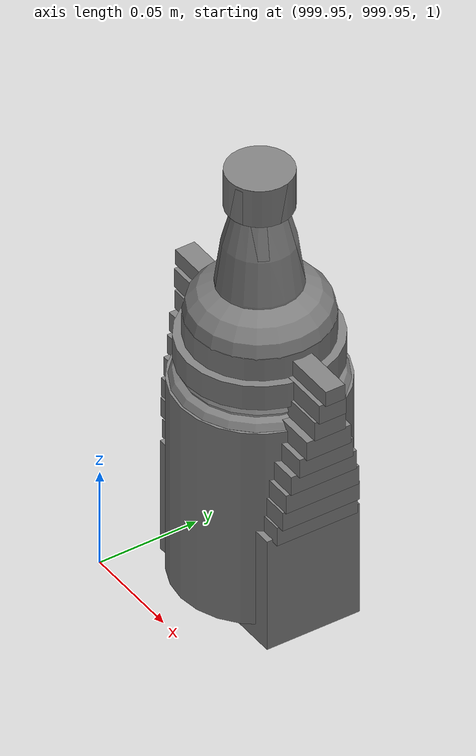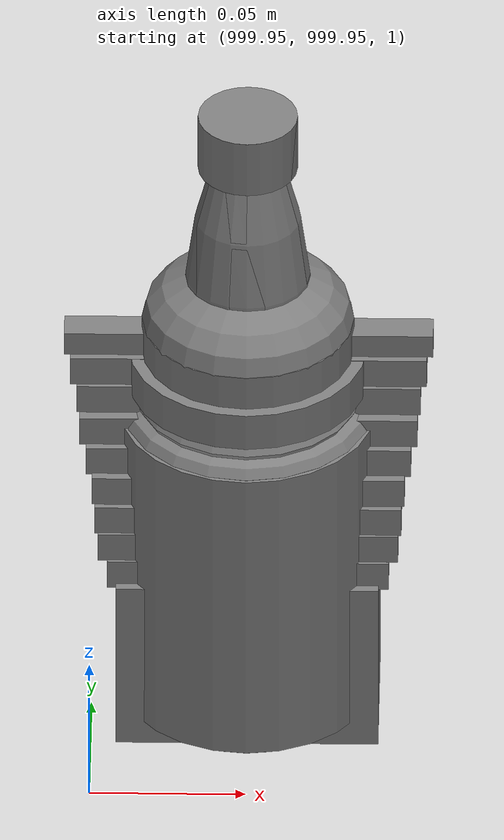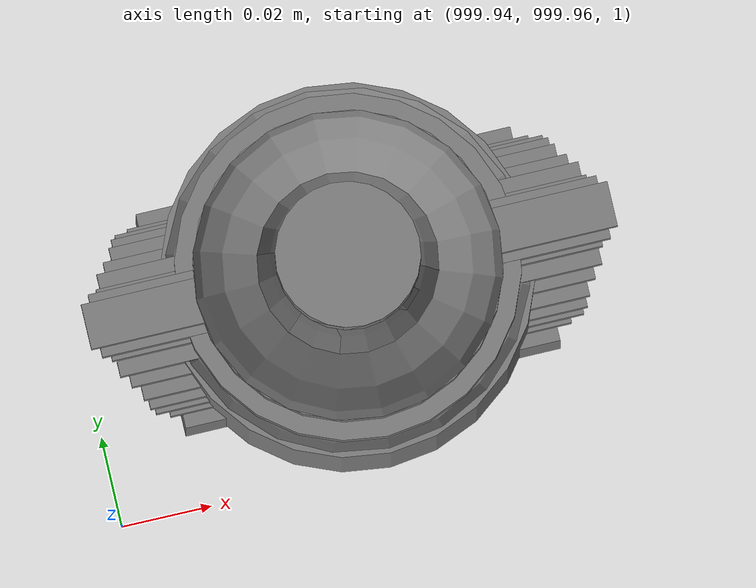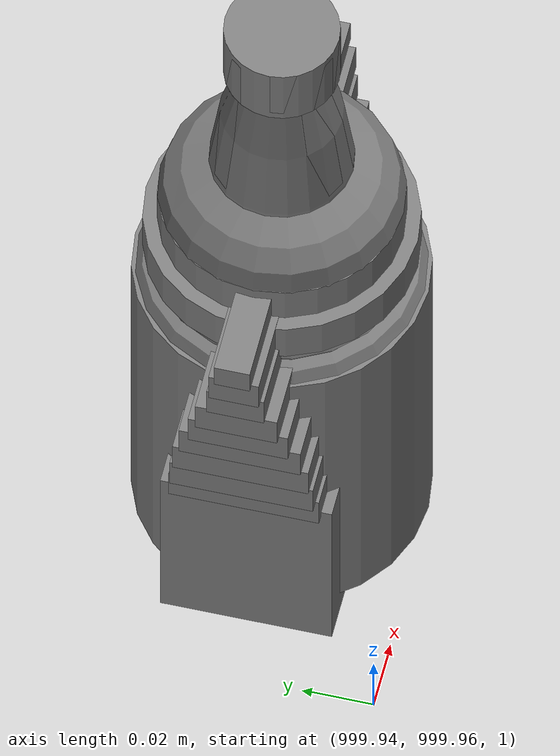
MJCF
<mujoco>
    <option gravity="0.000000000 0.000000000 -9.810000420" timestep="0.0166666" integrator="implicitfast" density="1.225" viscosity="1.8000001e-05" noslip_iterations="10" iterations="100" sdf_iterations="50">
        <flag multiccd="disable"/>
    </option>
    <size memory="1000M"/>
    <compiler coordinate="local"/>
    <worldbody>
        <light cutoff="30" pos="0 1 1" dir="0 -1 -2"/>
        <light cutoff="30" pos="0 -1 1" dir="0 1 -2"/>
        <body pos="-7.168000221 2.823999882 1.227496982" euler="-0.283413976 0.056829724 -0.133293271" name="openloong_gripper_2f85_fix_base_usda_Pos">
            <geom contype="1" conaffinity="1" density="1000" type="box" material="" rgba="0.500000000 0.500000000 0.500000000 1.000000000" solimp="0.899999976 0.949999988 0.001000000" friction="1.000000000 0.005000000 0.000100000" solref="0.020000000 1.000000000" margin="0" condim="3" group="0" pos="-0.002278805 0.074524641 -0.004134059" quat="0.315989345 0.948763072 -0.000000000 0.000000000" size="0.059999999 0.013000000 0.035000000" name="openloong_gripper_2f85_fix_base_usda_geom_DF37DCAF_033C_4A2B_AD20_34AA223257DA"/>
            <geom contype="1" conaffinity="1" density="1000" type="box" material="" rgba="0.500000000 0.500000000 0.500000000 1.000000000" solimp="0.899999976 0.949999988 0.001000000" friction="1.000000000 0.005000000 0.000100000" solref="0.020000000 1.000000000" margin="0" condim="3" group="0" pos="-0.002278805 0.078031301 0.008128285" quat="0.990447521 -0.137893379 -0.000000000 -0.000000000" size="0.059999999 0.010000000 0.035000000" name="openloong_gripper_2f85_fix_base_usda_geom_1284621A_5814_4B43_A3D1_540C189452F6"/>
            <geom contype="1" conaffinity="1" density="1000" type="box" material="" rgba="0.500000000 0.500000000 0.500000000 1.000000000" solimp="0.899999976 0.949999988 0.001000000" friction="1.000000000 0.005000000 0.000100000" solref="0.020000000 1.000000000" margin="0" condim="3" group="0" pos="-0.002278805 0.080785275 -0.002596974" quat="0.287325472 -0.957833409 0.000000000 -0.000000000" size="0.059999999 0.013000000 0.035000000" name="openloong_gripper_2f85_fix_base_usda_geom_B13D510A_0BD6_4336_A757_7B51D39CF23F"/>
            <geom contype="1" conaffinity="1" density="1000" type="box" material="" rgba="0.500000000 0.500000000 0.500000000 1.000000000" solimp="0.899999976 0.949999988 0.001000000" friction="1.000000000 0.005000000 0.000100000" solref="0.020000000 1.000000000" margin="0" condim="3" group="0" pos="-0.002278805 -0.098804474 -0.020146966" quat="0.988851666 0.148906454 0.000000000 -0.000000000" size="0.059999999 0.022000000 0.020000000" name="openloong_gripper_2f85_fix_base_usda_geom_96BD9423_2085_44DC_A862_BA61477147E9"/>
            <geom contype="1" conaffinity="1" density="1000" type="box" material="" rgba="0.500000000 0.500000000 0.500000000 1.000000000" solimp="0.899999976 0.949999988 0.001000000" friction="1.000000000 0.005000000 0.000100000" solref="0.020000000 1.000000000" margin="0" condim="3" group="0" pos="-0.002279282 0.019920111 0.012102962" quat="0.995421767 0.095583342 -0.000000000 -0.000000000" size="0.059999999 0.025000000 0.026000001" name="openloong_gripper_2f85_fix_base_usda_geom_CBD291C3_246E_4A08_B8F6_9EEA7B7ECE51"/>
            <geom contype="1" conaffinity="1" density="1000" type="box" material="" rgba="0.500000000 0.500000000 0.500000000 1.000000000" solimp="0.899999976 0.949999988 0.001000000" friction="1.000000000 0.005000000 0.000100000" solref="0.020000000 1.000000000" margin="0" condim="3" group="0" pos="-0.002279282 0.005734444 -0.014276862" quat="0.999571741 -0.029275302 -0.000000000 -0.000000000" size="0.059999999 0.050000001 0.010000000" name="openloong_gripper_2f85_fix_base_usda_geom_7EDCDB15_C72E_4010_A5E6_DE470E338658"/>
            <geom contype="1" conaffinity="1" density="1000" type="box" material="" rgba="0.500000000 0.500000000 0.500000000 1.000000000" solimp="0.899999976 0.949999988 0.001000000" friction="1.000000000 0.005000000 0.000100000" solref="0.020000000 1.000000000" margin="0" condim="3" group="0" pos="-0.002278805 0.079460382 0.007771969" quat="0.922590554 -0.385781586 0.000000000 -0.000000000" size="0.059999999 0.010000000 0.035000000" name="openloong_gripper_2f85_fix_base_usda_geom_409BDCB9_614F_4948_A41B_7F369509790F"/>
            <geom contype="1" conaffinity="1" density="1000" type="box" material="" rgba="0.500000000 0.500000000 0.500000000 1.000000000" solimp="0.899999976 0.949999988 0.001000000" friction="1.000000000 0.005000000 0.000100000" solref="0.020000000 1.000000000" margin="0" condim="3" group="0" pos="-0.002279282 0.081384182 -0.001320124" quat="0.590483785 -0.807049930 0.000000000 -0.000000000" size="0.059999999 0.013000000 0.035000000" name="openloong_gripper_2f85_fix_base_usda_geom_BA64A0B2_B9CE_491E_AD5E_F4AF1F788912"/>
            <geom contype="1" conaffinity="1" density="1000" type="box" material="" rgba="0.500000000 0.500000000 0.500000000 1.000000000" solimp="0.899999976 0.949999988 0.001000000" friction="1.000000000 0.005000000 0.000100000" solref="0.020000000 1.000000000" margin="0" condim="3" group="0" pos="-0.002278805 -0.059297800 -0.007972836" quat="0.988851666 0.148906454 0.000000000 -0.000000000" size="0.059999999 0.020000000 0.022000000" name="openloong_gripper_2f85_fix_base_usda_geom_8722731D_E89D_49C4_8EAE_1134A3A9AF4B"/>
            <geom contype="1" conaffinity="1" density="1000" type="box" material="" rgba="0.500000000 0.500000000 0.500000000 1.000000000" solimp="0.899999976 0.949999988 0.001000000" friction="1.000000000 0.005000000 0.000100000" solref="0.020000000 1.000000000" margin="0" condim="3" group="0" pos="-0.002278805 0.076618671 -0.004656792" quat="0.004634961 0.999989629 -0.000000000 0.000000000" size="0.059999999 0.013000000 0.035000000" name="openloong_gripper_2f85_fix_base_usda_geom_AD44299B_AABE_4CDE_B067_7BFCC41F0738"/>
            <geom contype="1" conaffinity="1" density="1000" type="box" material="" rgba="0.500000000 0.500000000 0.500000000 1.000000000" solimp="0.899999976 0.949999988 0.001000000" friction="1.000000000 0.005000000 0.000100000" solref="0.020000000 1.000000000" margin="0" condim="3" group="0" pos="-0.002279282 -0.021952629 0.002960086" quat="0.991270423 0.131847665 -0.000000000 0.000000000" size="0.059999999 0.020000000 0.024000000" name="openloong_gripper_2f85_fix_base_usda_geom_A2C00F60_46E2_4E21_8B0D_55D9DFED4AA4"/>
            <geom contype="1" conaffinity="1" density="1000" type="box" material="" rgba="0.500000000 0.500000000 0.500000000 1.000000000" solimp="0.899999976 0.949999988 0.001000000" friction="1.000000000 0.005000000 0.000100000" solref="0.020000000 1.000000000" margin="0" condim="3" group="0" pos="-0.002278805 0.081418991 0.002587914" quat="0.803492308 -0.595315695 0.000000000 -0.000000000" size="0.059999999 0.013000000 0.035000000" name="openloong_gripper_2f85_fix_base_usda_geom_C52A3CE3_3810_4702_BD5A_763D7152CD69"/>
            <geom contype="1" conaffinity="1" density="1000" type="box" material="" rgba="0.500000000 0.500000000 0.500000000 1.000000000" solimp="0.899999976 0.949999988 0.001000000" friction="1.000000000 0.005000000 0.000100000" solref="0.020000000 1.000000000" margin="0" condim="3" group="0" pos="-0.002278805 0.061115503 0.008545756" quat="0.999326169 0.036714450 0.000000000 -0.000000000" size="0.059999999 0.020000000 0.035000000" name="openloong_gripper_2f85_fix_base_usda_geom_4BF37218_BC99_401B_889B_38DE46B10C6B"/>
            <freejoint name="openloong_gripper_2f85_fix_base_usda_pos_scan"/>
        </body>
        <body pos="1000.000000000 1000.000000000 1.000000000" euler="0.000000000 0.000000000 0.000000000" name="openloong_gripper_2f85_fix_base_usda_bottle_red">
            <geom contype="1" conaffinity="1" density="1000" type="ellipsoid" material="" rgba="0.500000000 0.500000000 0.500000000 1.000000000" solimp="0.899999976 0.949999988 0.001000000" friction="1.000000000 0.005000000 0.000100000" solref="0.020000000 1.000000000" margin="0" condim="3" group="0" pos="0.000000000 0.000000000 0.144284487" quat="1.000000000 0.000000000 0.000000000 0.000000000" size="0.021000000 0.021000000 0.079999998" name="openloong_gripper_2f85_fix_base_usda_geom_F6137B23_12E8_46AB_90D9_CE7498B5F4D2"/>
            <geom contype="1" conaffinity="1" density="1000" type="cylinder" material="" rgba="0.500000000 0.500000000 0.500000000 1.000000000" solimp="0.899999976 0.949999988 0.001000000" friction="1.000000000 0.005000000 0.000100000" solref="0.020000000 1.000000000" margin="0" condim="3" group="0" pos="0.000000000 0.000000000 0.220618963" quat="1.000000000 0.000000000 0.000000000 0.000000000" size="0.016000001 0.010000000 1.000000000" name="openloong_gripper_2f85_fix_base_usda_geom_CE63D93A_DC32_4B35_8EF0_D2837BCF238B"/>
            <geom contype="1" conaffinity="1" density="1000" type="ellipsoid" material="" rgba="0.500000000 0.500000000 0.500000000 1.000000000" solimp="0.899999976 0.949999988 0.001000000" friction="1.000000000 0.005000000 0.000100000" solref="0.020000000 1.000000000" margin="0" condim="3" group="0" pos="0.000000000 0.000000000 0.118945479" quat="1.000000000 0.000000000 0.000000000 0.000000000" size="0.030999999 0.030999999 0.029999999" name="openloong_gripper_2f85_fix_base_usda_geom_82FCA724_4627_4991_A3CF_0EE84AAD22F2"/>
            <geom contype="1" conaffinity="1" density="1000" type="box" material="" rgba="0.500000000 0.500000000 0.500000000 1.000000000" solimp="0.899999976 0.949999988 0.001000000" friction="1.000000000 0.005000000 0.000100000" solref="0.020000000 1.000000000" margin="0" condim="3" group="0" pos="0.000000000 0.000000000 0.002189159" quat="1.000000000 0.000000000 0.000000000 0.000000000" size="0.020000000 0.020000000 0.003000000" name="openloong_gripper_2f85_fix_base_usda_geom_5939F301_147A_42D4_9806_CDBE7419430A"/>
            <geom contype="1" conaffinity="1" density="1000" type="cylinder" material="" rgba="0.500000000 0.500000000 0.500000000 1.000000000" solimp="0.899999976 0.949999988 0.001000000" friction="1.000000000 0.005000000 0.000100000" solref="0.020000000 1.000000000" margin="0" condim="3" group="0" pos="0.000000000 -0.000366211 0.060884237" quat="1.000000000 0.000000000 0.000000000 0.000000000" size="0.030999999 0.057999998 1.000000000" name="openloong_gripper_2f85_fix_base_usda_geom_36F3A0CA_DC9B_4700_A4BD_72ACBF61D010"/>
            <freejoint name="openloong_gripper_2f85_fix_base_usda_bottle_red_joint"/>
            <site size="0.005000000 0.005000000 0.005000000" rgba="0.500000000 0.500000000 0.500000000 1.000000000" pos="0.000000000 0.000000000 0.000000000" quat="0.999961913 0.008726535 0.000000000 0.000000000" group="0" type="sphere" name="openloong_gripper_2f85_fix_base_usda_bottle_redsite"/>
        </body>
        <body pos="1000.000000000 1000.000000000 1.000000000" euler="0.000000000 0.000000000 0.000000000" name="openloong_gripper_2f85_fix_base_usda_bottle_blue">
            <geom contype="1" conaffinity="1" density="1000" type="ellipsoid" material="" rgba="0.500000000 0.500000000 0.500000000 1.000000000" solimp="0.899999976 0.949999988 0.001000000" friction="1.000000000 0.005000000 0.000100000" solref="0.020000000 1.000000000" margin="0" condim="3" group="0" pos="0.000000000 0.000000000 0.118920922" quat="1.000000000 0.000000000 0.000000000 0.000000000" size="0.030999999 0.030999999 0.029999999" name="openloong_gripper_2f85_fix_base_usda_geom_192FBCF3_F232_44CD_ACBC_2BB55264A617"/>
            <geom contype="1" conaffinity="1" density="1000" type="box" material="" rgba="0.500000000 0.500000000 0.500000000 1.000000000" solimp="0.899999976 0.949999988 0.001000000" friction="1.000000000 0.005000000 0.000100000" solref="0.020000000 1.000000000" margin="0" condim="3" group="0" pos="0.000000000 0.000000000 0.002164602" quat="1.000000000 0.000000000 0.000000000 0.000000000" size="0.020000000 0.020000000 0.003000000" name="openloong_gripper_2f85_fix_base_usda_geom_EECADE84_AACE_4C15_A0CF_F6B7E291B5C3"/>
            <geom contype="1" conaffinity="1" density="1000" type="cylinder" material="" rgba="0.500000000 0.500000000 0.500000000 1.000000000" solimp="0.899999976 0.949999988 0.001000000" friction="1.000000000 0.005000000 0.000100000" solref="0.020000000 1.000000000" margin="0" condim="3" group="0" pos="0.000000000 -0.000366211 0.060859680" quat="1.000000000 0.000000000 0.000000000 0.000000000" size="0.030999999 0.057999998 1.000000000" name="openloong_gripper_2f85_fix_base_usda_geom_DB8F3574_17EB_43DA_9F2C_44FD01D750A3"/>
            <geom contype="1" conaffinity="1" density="1000" type="cylinder" material="" rgba="0.500000000 0.500000000 0.500000000 1.000000000" solimp="0.899999976 0.949999988 0.001000000" friction="1.000000000 0.005000000 0.000100000" solref="0.020000000 1.000000000" margin="0" condim="3" group="0" pos="0.000000000 0.000000000 0.220594406" quat="1.000000000 0.000000000 0.000000000 0.000000000" size="0.016000001 0.010000000 1.000000000" name="openloong_gripper_2f85_fix_base_usda_geom_B2500691_93DE_4CB3_94AD_88EA93C78A54"/>
            <geom contype="1" conaffinity="1" density="1000" type="ellipsoid" material="" rgba="0.500000000 0.500000000 0.500000000 1.000000000" solimp="0.899999976 0.949999988 0.001000000" friction="1.000000000 0.005000000 0.000100000" solref="0.020000000 1.000000000" margin="0" condim="3" group="0" pos="0.000000000 0.000000000 0.144259930" quat="1.000000000 0.000000000 0.000000000 0.000000000" size="0.021000000 0.021000000 0.079999998" name="openloong_gripper_2f85_fix_base_usda_geom_1FDBE58A_5901_4C57_B570_5F595564CD4C"/>
            <freejoint name="openloong_gripper_2f85_fix_base_usda_bottle_blue_joint"/>
            <site size="0.005000000 0.005000000 0.005000000" rgba="0.500000000 0.500000000 0.500000000 1.000000000" pos="0.000000000 0.000000000 0.000000000" quat="0.999961913 0.008726535 0.000000000 0.000000000" group="0" type="sphere" name="openloong_gripper_2f85_fix_base_usda_bottle_bluesite"/>
        </body>
        <body pos="-1.785953283 5.762605667 1.806289077" euler="6.955086708 24.635330200 -97.471206665" mocap="true" name="spotlight3_SpotLight"/>
        <body pos="1000.000000000 1000.000000000 1.000000000" euler="0.000000000 0.000000000 0.000000000" name="openloong_gripper_2f85_fix_base_usda_salt">
            <geom contype="1" conaffinity="1" density="1000" type="box" material="" rgba="0.500000000 0.500000000 0.500000000 1.000000000" solimp="0.899999976 0.949999988 0.001000000" friction="1.000000000 0.005000000 0.000100000" solref="0.020000000 1.000000000" margin="0" condim="3" group="0" pos="0.000305176 0.000000000 0.084862232" quat="1.000000000 0.000000000 0.000000000 0.000000000" size="0.048999999 0.018999999 0.005000000" name="openloong_gripper_2f85_fix_base_usda_geom_30132A9E_5F84_4F19_AA0F_5355C081F363"/>
            <geom contype="1" conaffinity="1" density="1000" type="box" material="" rgba="0.500000000 0.500000000 0.500000000 1.000000000" solimp="0.899999976 0.949999988 0.001000000" friction="1.000000000 0.005000000 0.000100000" solref="0.020000000 1.000000000" margin="0" condim="3" group="0" pos="0.000305176 0.000000000 0.104564309" quat="1.000000000 0.000000000 0.000000000 0.000000000" size="0.052000001 0.014000000 0.005000000" name="openloong_gripper_2f85_fix_base_usda_geom_0CA22530_B44E_4ECB_9E84_33D2D4B71AF0"/>
            <geom contype="1" conaffinity="1" density="1000" type="box" material="" rgba="0.500000000 0.500000000 0.500000000 1.000000000" solimp="0.899999976 0.949999988 0.001000000" friction="1.000000000 0.005000000 0.000100000" solref="0.020000000 1.000000000" margin="0" condim="3" group="0" pos="0.000305176 0.000000000 0.114487171" quat="1.000000000 0.000000000 0.000000000 0.000000000" size="0.054000001 0.011500000 0.005000000" name="openloong_gripper_2f85_fix_base_usda_geom_7B3AE0B8_0C76_481C_BBA3_181AE38DCFE0"/>
            <geom contype="1" conaffinity="1" density="1000" type="box" material="" rgba="0.500000000 0.500000000 0.500000000 1.000000000" solimp="0.899999976 0.949999988 0.001000000" friction="1.000000000 0.005000000 0.000100000" solref="0.020000000 1.000000000" margin="0" condim="3" group="0" pos="0.000305176 0.000000000 0.075103164" quat="1.000000000 0.000000000 0.000000000 0.000000000" size="0.048000000 0.020000000 0.005000000" name="openloong_gripper_2f85_fix_base_usda_geom_D2513928_CFF0_48C2_B745_388DFE997FBE"/>
            <geom contype="1" conaffinity="1" density="1000" type="box" material="" rgba="0.500000000 0.500000000 0.500000000 1.000000000" solimp="0.899999976 0.949999988 0.001000000" friction="1.000000000 0.005000000 0.000100000" solref="0.020000000 1.000000000" margin="0" condim="3" group="0" pos="0.000305176 0.000000000 0.134892464" quat="1.000000000 0.000000000 0.000000000 0.000000000" size="0.057000000 0.007000000 0.005000000" name="openloong_gripper_2f85_fix_base_usda_geom_F3574AEC_9CF7_4377_9629_1E3C1AE47D74"/>
            <geom contype="1" conaffinity="1" density="1000" type="box" material="" rgba="0.500000000 0.500000000 0.500000000 1.000000000" solimp="0.899999976 0.949999988 0.001000000" friction="1.000000000 0.005000000 0.000100000" solref="0.020000000 1.000000000" margin="0" condim="3" group="0" pos="0.000305176 0.000000000 0.094920278" quat="1.000000000 0.000000000 0.000000000 0.000000000" size="0.050000001 0.017000001 0.005000000" name="openloong_gripper_2f85_fix_base_usda_geom_7B8AE398_D556_42C8_A0EC_CC50E2318478"/>
            <geom contype="1" conaffinity="1" density="1000" type="box" material="" rgba="0.500000000 0.500000000 0.500000000 1.000000000" solimp="0.899999976 0.949999988 0.001000000" friction="1.000000000 0.005000000 0.000100000" solref="0.020000000 1.000000000" margin="0" condim="3" group="0" pos="0.000305176 0.000000000 0.065204859" quat="1.000000000 0.000000000 0.000000000 0.000000000" size="0.045000002 0.021000000 0.005000000" name="openloong_gripper_2f85_fix_base_usda_geom_14611A27_EDE6_446C_AC35_5B6168071463"/>
            <geom contype="1" conaffinity="1" density="1000" type="box" material="" rgba="0.500000000 0.500000000 0.500000000 1.000000000" solimp="0.899999976 0.949999988 0.001000000" friction="1.000000000 0.005000000 0.000100000" solref="0.020000000 1.000000000" margin="0" condim="3" group="0" pos="0.000305176 0.000000000 0.144135714" quat="1.000000000 0.000000000 0.000000000 0.000000000" size="0.059000000 0.005000000 0.004000000" name="openloong_gripper_2f85_fix_base_usda_geom_DC2C7CEB_3FD5_4168_8F91_06EFB56C9955"/>
            <geom contype="1" conaffinity="1" density="1000" type="box" material="" rgba="0.500000000 0.500000000 0.500000000 1.000000000" solimp="0.899999976 0.949999988 0.001000000" friction="1.000000000 0.005000000 0.000100000" solref="0.020000000 1.000000000" margin="0" condim="3" group="0" pos="0.000000000 0.000000000 0.031593561" quat="1.000000000 0.000000000 0.000000000 0.000000000" size="0.041999999 0.024000000 0.029999999" name="openloong_gripper_2f85_fix_base_usda_geom_ADA6876E_12BF_45BA_90EB_958963AE5F7F"/>
            <geom contype="1" conaffinity="1" density="1000" type="box" material="" rgba="0.500000000 0.500000000 0.500000000 1.000000000" solimp="0.899999976 0.949999988 0.001000000" friction="1.000000000 0.005000000 0.000100000" solref="0.020000000 1.000000000" margin="0" condim="3" group="0" pos="0.000305176 0.000000000 0.124608755" quat="1.000000000 0.000000000 0.000000000 0.000000000" size="0.055000000 0.008000000 0.005000000" name="openloong_gripper_2f85_fix_base_usda_geom_20F344A7_3334_4085_9B08_333047A7B413"/>
            <freejoint name="openloong_gripper_2f85_fix_base_usda_salt_joint"/>
            <site size="0.005000000 0.005000000 0.005000000" rgba="0.500000000 0.500000000 0.500000000 1.000000000" pos="0.000000000 0.000000000 0.000000000" quat="1.000000000 0.000000000 0.000000000 0.000000000" group="0" type="sphere" name="openloong_gripper_2f85_fix_base_usda_saltsite"/>
        </body>
        <body pos="1000.000000000 1000.000000000 1.000000000" euler="0.000000000 0.000000000 0.000000000" name="openloong_gripper_2f85_fix_base_usda_jar_01">
            <geom contype="1" conaffinity="1" density="1000" type="box" material="" rgba="0.500000000 0.500000000 0.500000000 1.000000000" solimp="0.899999976 0.949999988 0.001000000" friction="1.000000000 0.005000000 0.000100000" solref="0.020000000 1.000000000" margin="0" condim="3" group="0" pos="0.000000000 0.000000000 0.006158113" quat="1.000000000 0.000000000 0.000000000 0.000000000" size="0.020000000 0.020000000 0.005000000" name="openloong_gripper_2f85_fix_base_usda_geom_87FCE729_B9BD_472A_A56D_75867CC00B59"/>
            <geom contype="1" conaffinity="1" density="1000" type="cylinder" material="" rgba="0.500000000 0.500000000 0.500000000 1.000000000" solimp="0.899999976 0.949999988 0.001000000" friction="1.000000000 0.005000000 0.000100000" solref="0.020000000 1.000000000" margin="0" condim="3" group="0" pos="0.000000000 0.000000000 0.062744498" quat="1.000000000 0.000000000 0.000000000 0.000000000" size="0.041000001 0.052999999 1.000000000" name="openloong_gripper_2f85_fix_base_usda_geom_BAEA9689_DF10_49EF_B0AB_0C0F7D0EDDDA"/>
            <geom contype="1" conaffinity="1" density="1000" type="ellipsoid" material="" rgba="0.500000000 0.500000000 0.500000000 1.000000000" solimp="0.899999976 0.949999988 0.001000000" friction="1.000000000 0.005000000 0.000100000" solref="0.020000000 1.000000000" margin="0" condim="3" group="0" pos="0.000000000 0.000000000 0.122252703" quat="1.000000000 0.000000000 0.000000000 0.000000000" size="0.035999998 0.035999998 0.010000000" name="openloong_gripper_2f85_fix_base_usda_geom_E80DA7F8_BD98_4A93_A8D8_750A63464E34"/>
            <geom contype="1" conaffinity="1" density="1000" type="cylinder" material="" rgba="0.500000000 0.500000000 0.500000000 1.000000000" solimp="0.899999976 0.949999988 0.001000000" friction="1.000000000 0.005000000 0.000100000" solref="0.020000000 1.000000000" margin="0" condim="3" group="0" pos="0.000000000 0.000000000 0.015747190" quat="1.000000000 0.000000000 0.000000000 0.000000000" size="0.035000000 0.010000000 1.000000000" name="openloong_gripper_2f85_fix_base_usda_geom_C5C8360C_EC6A_4C9C_84D3_46354DF074B7"/>
            <geom contype="1" conaffinity="1" density="1000" type="ellipsoid" material="" rgba="0.500000000 0.500000000 0.500000000 1.000000000" solimp="0.899999976 0.949999988 0.001000000" friction="1.000000000 0.005000000 0.000100000" solref="0.020000000 1.000000000" margin="0" condim="3" group="0" pos="0.000000000 0.000000000 0.115815401" quat="1.000000000 0.000000000 0.000000000 0.000000000" size="0.039999999 0.039999999 0.010000000" name="openloong_gripper_2f85_fix_base_usda_geom_F4DF345A_8C35_4CFD_9220_E926828FB54A"/>
            <geom contype="1" conaffinity="1" density="1000" type="cylinder" material="" rgba="0.500000000 0.500000000 0.500000000 1.000000000" solimp="0.899999976 0.949999988 0.001000000" friction="1.000000000 0.005000000 0.000100000" solref="0.020000000 1.000000000" margin="0" condim="3" group="0" pos="0.000000000 0.000000000 0.133183479" quat="1.000000000 0.000000000 0.000000000 0.000000000" size="0.037999999 0.006500000 1.000000000" name="openloong_gripper_2f85_fix_base_usda_geom_3202BB69_40B2_4219_8DD5_E47C24B8122A"/>
            <freejoint name="openloong_gripper_2f85_fix_base_usda_jar_01_joint"/>
            <site size="0.005000000 0.005000000 0.005000000" rgba="0.500000000 0.500000000 0.500000000 1.000000000" pos="0.000000000 0.000000000 0.000000000" quat="1.000000000 0.000000000 0.000000000 0.000000000" group="0" type="sphere" name="openloong_gripper_2f85_fix_base_usda_jar_01site"/>
        </body>
        <body pos="-1.862821102 6.244769573 1.727146506" euler="-81.793235779 54.808059692 -50.262943268" mocap="true" name="spotlight4_SpotLight"/>
        <body pos="-2.289836168 6.493119717 1.859532118" euler="84.554557800 -2.137010813 -152.421356201" mocap="true" name="spotlight2_SpotLight"/>
        <body pos="1000.000000000 1000.000000000 1.000000000" euler="0.000000000 0.000000000 0.000000000" name="openloong_gripper_2f85_fix_base_usda_can">
            <geom contype="1" conaffinity="1" density="1000" type="cylinder" material="" rgba="0.500000000 0.500000000 0.500000000 1.000000000" solimp="0.899999976 0.949999988 0.001000000" friction="1.000000000 0.005000000 0.000100000" solref="0.020000000 1.000000000" margin="0" condim="3" group="0" pos="0.000000000 0.000000000 0.079676986" quat="1.000000000 0.000000000 0.000000000 0.000000000" size="0.034000002 0.071999997 1.000000000" name="openloong_gripper_2f85_fix_base_usda_geom_C87466E1_B703_41E7_963B_971635703C9A"/>
            <geom contype="1" conaffinity="1" density="1000" type="ellipsoid" material="" rgba="0.500000000 0.500000000 0.500000000 1.000000000" solimp="0.899999976 0.949999988 0.001000000" friction="1.000000000 0.005000000 0.000100000" solref="0.020000000 1.000000000" margin="0" condim="3" group="0" pos="0.000000000 0.000000000 0.151854277" quat="1.000000000 0.000000000 0.000000000 0.000000000" size="0.034000002 0.034000002 0.020000000" name="openloong_gripper_2f85_fix_base_usda_geom_1F20E017_D70F_4063_93B5_75295D5E4EFA"/>
            <geom contype="1" conaffinity="1" density="1000" type="box" material="" rgba="0.500000000 0.500000000 0.500000000 1.000000000" solimp="0.899999976 0.949999988 0.001000000" friction="1.000000000 0.005000000 0.000100000" solref="0.020000000 1.000000000" margin="0" condim="3" group="0" pos="0.000000000 0.000000000 0.004777670" quat="1.000000000 0.000000000 0.000000000 0.000000000" size="0.020000000 0.020000000 0.005000000" name="openloong_gripper_2f85_fix_base_usda_geom_CCBAACC5_CFE7_480B_8C6E_109FFB0FB283"/>
            <freejoint name="openloong_gripper_2f85_fix_base_usda_can_joint"/>
            <site size="0.005000000 0.005000000 0.005000000" rgba="0.500000000 0.500000000 0.500000000 1.000000000" pos="0.000000000 0.000000000 0.000000000" quat="1.000000000 0.000000000 0.000000000 0.000000000" group="0" type="sphere" name="openloong_gripper_2f85_fix_base_usda_cansite"/>
        </body>
        <body pos="0.000000000 0.000000000 0.000000000" euler="0.000000000 0.000000000 0.000000000" name="Interactive Objects_Interactive Objects"/>
        <body pos="0.000000000 0.000000000 0.000000000" euler="0.000000000 0.000000000 0.000000000" name=" Static Objects_ Static Objects">
            <geom contype="1" conaffinity="1" density="1000" type="box" material="" rgba="0.500000000 0.500000000 0.500000000 1.000000000" solimp="0.899999976 0.949999988 0.001000000" friction="1.000000000 0.005000000 0.000100000" solref="0.020000000 1.000000000" margin="0" condim="3" group="0" pos="-6.286010742 6.153595448 1.563861728" quat="0.707107067 0.000000000 0.000000000 0.707106471" size="0.529999971 3.134999990 0.025000000" name=" Static Objects_geom_09A4C5AF_4CDD_40FE_B59E_E8624FDC893B"/>
            <geom contype="1" conaffinity="1" density="1000" type="box" material="" rgba="0.500000000 0.500000000 0.500000000 1.000000000" solimp="0.899999976 0.949999988 0.001000000" friction="1.000000000 0.005000000 0.000100000" solref="0.020000000 1.000000000" margin="0" condim="3" group="0" pos="-3.101639986 6.150595188 1.018643856" quat="1.000000000 0.000000000 0.000000000 0.000000000" size="0.050000001 0.579999983 1.019999981" name=" Static Objects_geom_F9293DAC_B918_4037_AC83_F8A4DE99A224"/>
            <geom contype="1" conaffinity="1" density="1000" type="box" material="" rgba="0.500000000 0.500000000 0.500000000 1.000000000" solimp="0.899999976 0.949999988 0.001000000" friction="1.000000000 0.005000000 0.000100000" solref="0.020000000 1.000000000" margin="0" condim="3" group="0" pos="-2.825197220 6.153595448 1.563861728" quat="0.707107067 0.000000000 0.000000000 0.707106471" size="0.550000012 0.239999995 0.025000000" name=" Static Objects_geom_6C8E3C0B_23BE_419C_9977_5168F62E4624"/>
            <geom contype="1" conaffinity="1" density="1000" type="box" material="" rgba="0.500000000 0.500000000 0.500000000 1.000000000" solimp="0.899999976 0.949999988 0.001000000" friction="1.000000000 0.005000000 0.000100000" solref="0.020000000 1.000000000" margin="0" condim="3" group="0" pos="-6.311686516 6.153595448 1.018643856" quat="0.707107067 0.000000000 0.000000000 0.707106471" size="0.050000001 3.150000095 1.019999981" name=" Static Objects_geom_A27A8297_485A_4A3D_AFAE_BF42169792AA"/>
            <geom contype="1" conaffinity="1" density="1000" type="box" material="" rgba="0.500000000 0.500000000 0.500000000 1.000000000" solimp="0.899999976 0.949999988 0.001000000" friction="1.000000000 0.005000000 0.000100000" solref="0.020000000 1.000000000" margin="0" condim="3" group="0" pos="-2.825197220 6.153595448 1.115278244" quat="0.707107067 0.000000000 0.000000000 0.707106471" size="0.550000012 0.239999995 0.025000000" name=" Static Objects_geom_F1861110_2B5B_43F6_B23F_5BFD1988897F"/>
            <geom contype="1" conaffinity="1" density="1000" type="box" material="" rgba="0.500000000 0.500000000 0.500000000 1.000000000" solimp="0.899999976 0.949999988 0.001000000" friction="1.000000000 0.005000000 0.000100000" solref="0.020000000 1.000000000" margin="0" condim="3" group="0" pos="-6.293097973 6.153595448 1.114443064" quat="0.707107067 0.000000000 0.000000000 0.707106471" size="0.529999971 3.134999990 0.025000000" name=" Static Objects_geom_8694D578_8C1C_4B85_A5CD_D62FC2DC3608"/>
            <geom contype="1" conaffinity="1" density="1000" type="box" material="" rgba="0.500000000 0.500000000 0.500000000 1.000000000" solimp="0.899999976 0.949999988 0.001000000" friction="1.000000000 0.005000000 0.000100000" solref="0.020000000 1.000000000" margin="0" condim="3" group="0" pos="-2.825197220 6.153595448 0.629031777" quat="0.707107067 0.000000000 0.000000000 0.707106471" size="0.550000012 0.239999995 0.025000000" name=" Static Objects_geom_2599CA2D_37A4_4AAA_962E_2FF89D637AE3"/>
            <geom contype="1" conaffinity="1" density="1000" type="box" material="" rgba="0.500000000 0.500000000 0.500000000 1.000000000" solimp="0.899999976 0.949999988 0.001000000" friction="1.000000000 0.005000000 0.000100000" solref="0.020000000 1.000000000" margin="0" condim="3" group="0" pos="-6.286010742 6.153595448 0.096129179" quat="0.707107067 0.000000000 0.000000000 0.707106471" size="0.529999971 3.134999990 0.098999999" name=" Static Objects_geom_FCA6F4FC_1186_49A4_9866_51FDB4232676"/>
            <geom contype="1" conaffinity="1" density="1000" type="box" material="" rgba="0.500000000 0.500000000 0.500000000 1.000000000" solimp="0.899999976 0.949999988 0.001000000" friction="1.000000000 0.005000000 0.000100000" solref="0.020000000 1.000000000" margin="0" condim="3" group="0" pos="-2.825197220 6.153595448 0.097434282" quat="0.707107067 0.000000000 0.000000000 0.707106471" size="0.550000012 0.239999995 0.098999999" name=" Static Objects_geom_3705DF4C_B70A_4088_A232_B48026736B0B"/>
            <geom contype="1" conaffinity="1" density="1000" type="box" material="" rgba="0.500000000 0.500000000 0.500000000 1.000000000" solimp="0.899999976 0.949999988 0.001000000" friction="1.000000000 0.005000000 0.000100000" solref="0.020000000 1.000000000" margin="0" condim="3" group="0" pos="-6.286010742 6.153595448 0.629031777" quat="0.707107067 0.000000000 0.000000000 0.707106471" size="0.529999971 3.134999990 0.025000000" name=" Static Objects_geom_A4501A98_4FDC_4CB9_87E9_C67678A7C454"/>
            <geom contype="1" conaffinity="1" density="1000" type="box" material="" rgba="0.500000000 0.500000000 0.500000000 1.000000000" solimp="0.899999976 0.949999988 0.001000000" friction="1.000000000 0.005000000 0.000100000" solref="0.020000000 1.000000000" margin="0" condim="3" group="0" pos="-6.000000000 20.159999847 2.000000000" quat="1.000000000 0.000000000 0.000000000 0.000000000" size="6.079999924 0.070000000 2.000000000" name=" Static Objects_geom_C39F2DBA_9102_42EF_93D6_ED099562B3D5"/>
            <geom contype="1" conaffinity="1" density="1000" type="box" material="" rgba="0.500000000 0.500000000 0.500000000 1.000000000" solimp="0.899999976 0.949999988 0.001000000" friction="1.000000000 0.005000000 0.000100000" solref="0.020000000 1.000000000" margin="0" condim="3" group="0" pos="-6.000000000 0.035000000 2.000000000" quat="1.000000000 0.000000000 0.000000000 0.000000000" size="6.079999924 0.070000000 2.000000000" name=" Static Objects_geom_6CAA4EAA_C65B_44F5_98A7_6371FD91EB42"/>
            <geom contype="1" conaffinity="1" density="1000" type="box" material="" rgba="0.500000000 0.500000000 0.500000000 1.000000000" solimp="0.899999976 0.949999988 0.001000000" friction="1.000000000 0.005000000 0.000100000" solref="0.020000000 1.000000000" margin="0" condim="3" group="0" pos="0.000000000 10.000000000 2.000000000" quat="1.000000000 0.000000000 0.000000000 0.000000000" size="0.070000000 10.500000000 2.000000000" name=" Static Objects_geom_8269D8E1_176C_4FE3_94CD_9C7C4BD1657D"/>
            <geom contype="1" conaffinity="1" density="1000" type="box" material="" rgba="0.500000000 0.500000000 0.500000000 1.000000000" solimp="0.899999976 0.949999988 0.001000000" friction="1.000000000 0.005000000 0.000100000" solref="0.020000000 1.000000000" margin="0" condim="3" group="0" pos="-12.050000191 10.000000000 2.000000000" quat="1.000000000 0.000000000 0.000000000 0.000000000" size="0.070000000 10.500000000 2.000000000" name=" Static Objects_geom_65F51E57_7667_4864_B28A_997086F2E0A1"/>
            <geom contype="1" conaffinity="1" density="1000" type="plane" material="" rgba="0.500000000 0.500000000 0.500000000 1.000000000" solimp="0.899999976 0.949999988 0.001000000" friction="1.000000000 0.005000000 0.000100000" solref="0.020000000 1.000000000" margin="0" condim="3" group="0" pos="-6.000000000 10.399999619 0.000000000" quat="1.000000000 0.000000000 0.000000000 0.000000000" size="6.050000191 10.800000191 0.010000000" name=" Static Objects_geom_895F095F_7AD0_4B7D_A1C1_312A45094505"/>
            <geom contype="1" conaffinity="1" density="1000" type="box" material="" rgba="0.500000000 0.500000000 0.500000000 1.000000000" solimp="0.899999976 0.949999988 0.001000000" friction="1.000000000 0.005000000 0.000100000" solref="0.020000000 1.000000000" margin="0" condim="3" group="0" pos="-8.830721855 2.096410990 0.549305558" quat="1.000000000 0.000000000 0.000000000 0.000000000" size="0.280000001 0.430000007 0.550000012" name=" Static Objects_geom_5F1E5CB0_C875_46F8_A700_19AC3FAAAFA9"/>
            <geom contype="1" conaffinity="1" density="1000" type="box" material="" rgba="0.500000000 0.500000000 0.500000000 1.000000000" solimp="0.899999976 0.949999988 0.001000000" friction="1.000000000 0.005000000 0.000100000" solref="0.020000000 1.000000000" margin="0" condim="3" group="0" pos="-6.460197449 2.937205315 0.548931718" quat="1.000000000 0.000000000 0.000000000 0.000000000" size="2.650000095 0.430000007 0.550000012" name=" Static Objects_geom_894F87A9_B85C_4A76_A6CE_E4DC3DB73C40"/>
            <geom contype="1" conaffinity="1" density="1000" type="box" material="" rgba="0.500000000 0.500000000 0.500000000 1.000000000" solimp="0.899999976 0.949999988 0.001000000" friction="1.000000000 0.005000000 0.000100000" solref="0.020000000 1.000000000" margin="0" condim="3" group="0" pos="-4.240264893 1.327049494 0.549888909" quat="1.000000000 0.000000000 0.000000000 0.000000000" size="0.430000007 1.200000048 0.550000012" name=" Static Objects_geom_EB0EEFE9_32BF_4DEE_9735_43AD3AA31CD2"/>
            <geom contype="1" conaffinity="1" density="1000" type="box" material="" rgba="0.500000000 0.500000000 0.500000000 1.000000000" solimp="0.899999976 0.949999988 0.001000000" friction="1.000000000 0.005000000 0.000100000" solref="0.020000000 1.000000000" margin="0" condim="3" group="0" pos="-7.408766270 3.088089943 1.776644945" quat="0.928051054 0.000000000 0.000000000 0.372453064" size="0.050000001 0.100000001 0.050000001" name=" Static Objects_geom_EB0DAFF8_56B3_45A1_B499_8B558E21EF12"/>
            <geom contype="1" conaffinity="1" density="1000" type="box" material="" rgba="0.500000000 0.500000000 0.500000000 1.000000000" solimp="0.899999976 0.949999988 0.001000000" friction="1.000000000 0.005000000 0.000100000" solref="0.020000000 1.000000000" margin="0" condim="3" group="0" pos="-7.437745571 3.067511320 1.289965630" quat="1.000000000 0.000000000 0.000000000 0.000000000" size="0.029999999 0.020000000 0.020000000" name=" Static Objects_geom_A3B4230E_5D60_4DA3_B65F_F1AB97906F62"/>
            <geom contype="1" conaffinity="1" density="1000" type="box" material="" rgba="0.500000000 0.500000000 0.500000000 1.000000000" solimp="0.899999976 0.949999988 0.001000000" friction="1.000000000 0.005000000 0.000100000" solref="0.020000000 1.000000000" margin="0" condim="3" group="0" pos="-7.719123363 2.867671013 1.173410416" quat="1.000000000 0.000000000 0.000000000 0.000000000" size="0.250000000 0.250000000 0.079999998" name=" Static Objects_geom_E3510260_25C1_46F3_AC22_7485FBF68152"/>
            <geom contype="1" conaffinity="1" density="1000" type="box" material="" rgba="0.500000000 0.500000000 0.500000000 1.000000000" solimp="0.899999976 0.949999988 0.001000000" friction="1.000000000 0.005000000 0.000100000" solref="0.020000000 1.000000000" margin="0" condim="3" group="0" pos="-7.719123363 2.958004713 1.530241251" quat="1.000000000 0.000000000 0.000000000 0.000000000" size="0.250000000 0.159999996 0.280000001" name=" Static Objects_geom_74450D40_C2AF_4C7D_A59D_FBF971F24D60"/>
            <geom contype="1" conaffinity="1" density="1000" type="cylinder" material="" rgba="0.500000000 0.500000000 0.500000000 1.000000000" solimp="0.899999976 0.949999988 0.001000000" friction="1.000000000 0.005000000 0.000100000" solref="0.020000000 1.000000000" margin="0" condim="3" group="0" pos="-7.427312374 3.069516420 1.502544641" quat="0.928051054 0.000000000 0.000000000 0.372453064" size="0.015000000 0.230000004 0.100000001" name=" Static Objects_geom_6AC7D035_F559_4350_893B_074F17C1A6C4"/>
            <geom contype="1" conaffinity="1" density="1000" type="box" material="" rgba="0.500000000 0.500000000 0.500000000 1.000000000" solimp="0.899999976 0.949999988 0.001000000" friction="1.000000000 0.005000000 0.000100000" solref="0.020000000 1.000000000" margin="0" condim="3" group="0" pos="-9.058088303 6.434794426 1.209077358" quat="1.000000000 0.000000000 0.000000000 0.000000000" size="0.250000000 0.100000001 0.070000000" name=" Static Objects_geom_C14BB668_2A28_46F9_97F6_13928EA22914"/>
            <geom contype="1" conaffinity="1" density="1000" type="box" material="" rgba="0.500000000 0.500000000 0.500000000 1.000000000" solimp="0.899999976 0.949999988 0.001000000" friction="1.000000000 0.005000000 0.000100000" solref="0.020000000 1.000000000" margin="0" condim="3" group="0" pos="-5.611940861 6.318420410 0.350975692" quat="1.000000000 0.000000000 0.000000000 0.000000000" size="0.699999988 0.100000001 0.150000006" name=" Static Objects_geom_55054E4D_CF09_4408_96E0_88F8431ACBA1"/>
            <geom contype="1" conaffinity="1" density="1000" type="box" material="" rgba="0.500000000 0.500000000 0.500000000 1.000000000" solimp="0.899999976 0.949999988 0.001000000" friction="1.000000000 0.005000000 0.000100000" solref="0.020000000 1.000000000" margin="0" condim="3" group="0" pos="-9.237723351 6.464855671 1.209077358" quat="1.000000000 0.000000000 0.000000000 0.000000000" size="0.100000001 0.100000001 0.070000000" name=" Static Objects_geom_BD74F6A1_05E5_4649_BA68_120E6508BB0D"/>
            <geom contype="1" conaffinity="1" density="1000" type="box" material="" rgba="0.500000000 0.500000000 0.500000000 1.000000000" solimp="0.899999976 0.949999988 0.001000000" friction="1.000000000 0.005000000 0.000100000" solref="0.020000000 1.000000000" margin="0" condim="3" group="0" pos="-6.300771236 6.459744930 1.744376063" quat="1.000000000 0.000000000 0.000000000 0.000000000" size="3.000000000 0.200000003 0.150000006" name=" Static Objects_geom_6D473ECE_57A7_4D5F_BB42_1E838CAD9A4F"/>
            <geom contype="1" conaffinity="1" density="1000" type="box" material="" rgba="0.500000000 0.500000000 0.500000000 1.000000000" solimp="0.899999976 0.949999988 0.001000000" friction="1.000000000 0.005000000 0.000100000" solref="0.020000000 1.000000000" margin="0" condim="3" group="0" pos="-7.373087406 6.458900928 1.214329123" quat="1.000000000 0.000000000 0.000000000 0.000000000" size="0.250000000 0.200000003 0.075000003" name=" Static Objects_geom_F1E3320E_C6BF_44FF_B259_4A93C74DB6CA"/>
            <geom contype="1" conaffinity="1" density="1000" type="box" material="" rgba="0.500000000 0.500000000 0.500000000 1.000000000" solimp="0.899999976 0.949999988 0.001000000" friction="1.000000000 0.005000000 0.000100000" solref="0.020000000 1.000000000" margin="0" condim="3" group="0" pos="-4.035642624 6.459744930 0.352518857" quat="1.000000000 0.000000000 0.000000000 0.000000000" size="0.800000012 0.200000003 0.150000006" name=" Static Objects_geom_2AFED904_1B1E_4466_8C94_614DF81E210F"/>
            <geom contype="1" conaffinity="1" density="1000" type="box" material="" rgba="0.500000000 0.500000000 0.500000000 1.000000000" solimp="0.899999976 0.949999988 0.001000000" friction="1.000000000 0.005000000 0.000100000" solref="0.020000000 1.000000000" margin="0" condim="3" group="0" pos="-3.907610416 6.318625927 0.800981164" quat="1.000000000 0.000000000 0.000000000 0.000000000" size="0.500000000 0.100000001 0.150000006" name=" Static Objects_geom_86D9C5D5_5590_48BA_8781_82650659C2AF"/>
            <geom contype="1" conaffinity="1" density="1000" type="box" material="" rgba="0.500000000 0.500000000 0.500000000 1.000000000" solimp="0.899999976 0.949999988 0.001000000" friction="1.000000000 0.005000000 0.000100000" solref="0.020000000 1.000000000" margin="0" condim="3" group="0" pos="-6.098561764 6.327973843 1.292199373" quat="1.000000000 0.000000000 0.000000000 0.000000000" size="0.500000000 0.100000001 0.150000006" name=" Static Objects_geom_E326E0E7_6B67_4D6D_B95F_1CD03FD4C8FC"/>
            <geom contype="1" conaffinity="1" density="1000" type="box" material="" rgba="0.500000000 0.500000000 0.500000000 1.000000000" solimp="0.899999976 0.949999988 0.001000000" friction="1.000000000 0.005000000 0.000100000" solref="0.020000000 1.000000000" margin="0" condim="3" group="0" pos="-7.886891365 6.459744930 0.352518857" quat="1.000000000 0.000000000 0.000000000 0.000000000" size="1.500000000 0.200000003 0.150000006" name=" Static Objects_geom_0BFA0ED8_DD45_4087_9EBA_59DDAB71B180"/>
            <geom contype="1" conaffinity="1" density="1000" type="box" material="" rgba="0.500000000 0.500000000 0.500000000 1.000000000" solimp="0.899999976 0.949999988 0.001000000" friction="1.000000000 0.005000000 0.000100000" solref="0.020000000 1.000000000" margin="0" condim="3" group="0" pos="-6.824534416 6.447464466 1.212718010" quat="1.000000000 0.000000000 0.000000000 0.000000000" size="0.100000001 0.100000001 0.075000003" name=" Static Objects_geom_FBE83FF1_BDDA_4791_91B9_FA4D67031C8C"/>
            <geom contype="1" conaffinity="1" density="1000" type="box" material="" rgba="0.500000000 0.500000000 0.500000000 1.000000000" solimp="0.899999976 0.949999988 0.001000000" friction="1.000000000 0.005000000 0.000100000" solref="0.020000000 1.000000000" margin="0" condim="3" group="0" pos="-4.407354832 6.459744930 1.292199373" quat="1.000000000 0.000000000 0.000000000 0.000000000" size="1.240000010 0.200000003 0.150000006" name=" Static Objects_geom_C072D200_C8F4_40B6_8BEA_70B2CB55B073"/>
            <geom contype="1" conaffinity="1" density="1000" type="box" material="" rgba="0.500000000 0.500000000 0.500000000 1.000000000" solimp="0.899999976 0.949999988 0.001000000" friction="1.000000000 0.005000000 0.000100000" solref="0.020000000 1.000000000" margin="0" condim="3" group="0" pos="-6.751636982 6.459744930 0.800981164" quat="1.000000000 0.000000000 0.000000000 0.000000000" size="2.200000048 0.200000003 0.150000006" name=" Static Objects_geom_47F54903_42CA_4298_9952_266E65665FA0"/>
            <geom contype="1" conaffinity="1" density="1000" type="box" material="" rgba="0.500000000 0.500000000 0.500000000 1.000000000" solimp="0.899999976 0.949999988 0.001000000" friction="1.000000000 0.005000000 0.000100000" solref="0.020000000 1.000000000" margin="0" condim="3" group="0" pos="-6.924745083 6.362090111 1.214329123" quat="1.000000000 0.000000000 0.000000000 0.000000000" size="0.200000003 0.100000001 0.075000003" name=" Static Objects_geom_710095A9_4A4D_422A_8C05_AA5BEB25A90C"/>
            <geom contype="1" conaffinity="1" density="1000" type="box" material="" rgba="0.500000000 0.500000000 0.500000000 1.000000000" solimp="0.899999976 0.949999988 0.001000000" friction="1.000000000 0.005000000 0.000100000" solref="0.020000000 1.000000000" margin="0" condim="3" group="0" pos="-8.844120979 6.464855671 1.209077358" quat="1.000000000 0.000000000 0.000000000 0.000000000" size="0.100000001 0.100000001 0.070000000" name=" Static Objects_geom_C912BF70_3EC2_46E3_9C2D_3D91E5A48281"/>
            <geom contype="1" conaffinity="1" density="1000" type="box" material="" rgba="0.500000000 0.500000000 0.500000000 1.000000000" solimp="0.899999976 0.949999988 0.001000000" friction="1.000000000 0.005000000 0.000100000" solref="0.020000000 1.000000000" margin="0" condim="3" group="0" pos="-3.157672644 6.136868477 1.348373055" quat="1.000000000 0.000000000 0.000000000 0.000000000" size="0.200000003 0.519999981 0.300000012" name=" Static Objects_geom_6CCD0B3C_7F4F_4FD3_84D9_41AEC4D47A92"/>
        </body>
        <body pos="-6.332345009 2.779978037 1.034067392" euler="0.000000000 0.000000000 0.000000000" name="openloong_gripper_2f85_fix_base_usda_basket">
            <geom contype="1" conaffinity="1" density="100000" type="box" material="" rgba="0.500000000 0.500000000 0.500000000 1.000000000" solimp="0.899999976 0.949999988 0.001000000" friction="1.000000000 0.899999976 0.000100000" solref="0.020000000 1.000000000" margin="0" condim="3" group="0" pos="-0.039724827 -0.188568115 0.167089701" quat="0.997537494 0.070135131 0.000000000 0.000000000" size="0.150000006 0.006000000 0.108000003" name="openloong_gripper_2f85_fix_base_usda_geom_6A53601F_D737_41FF_9904_DBD782F42EA1"/>
            <geom contype="1" conaffinity="1" density="100000" type="box" material="" rgba="0.500000000 0.500000000 0.500000000 1.000000000" solimp="0.899999976 0.949999988 0.001000000" friction="1.000000000 0.899999976 0.000100000" solref="0.020000000 1.000000000" margin="0" condim="3" group="0" pos="0.094372749 0.000000000 0.168361664" quat="0.706172049 0.036353335 0.036353379 0.706171215" size="0.200000003 0.006000000 0.108000003" name="openloong_gripper_2f85_fix_base_usda_geom_8359B742_0030_442A_AA13_004DFC425115"/>
            <geom contype="1" conaffinity="1" density="100000" type="box" material="" rgba="0.500000000 0.500000000 0.500000000 1.000000000" solimp="0.899999976 0.949999988 0.001000000" friction="1.000000000 0.899999976 0.000100000" solref="0.020000000 1.000000000" margin="0" condim="3" group="0" pos="-0.039724827 0.000000000 0.068126202" quat="1.000000000 0.000000000 0.000000000 0.000000000" size="0.129999995 0.174999997 0.006000000" name="openloong_gripper_2f85_fix_base_usda_geom_C5A7E205_8943_4BEB_86B8_7AE32F002D01"/>
            <geom contype="1" conaffinity="1" density="100000" type="box" material="" rgba="0.500000000 0.500000000 0.500000000 1.000000000" solimp="0.899999976 0.949999988 0.001000000" friction="1.000000000 0.899999976 0.000100000" solref="0.020000000 1.000000000" margin="0" condim="3" group="0" pos="-0.039724827 0.188377380 0.167089701" quat="0.997489929 -0.070808925 0.000000000 0.000000000" size="0.150000006 0.006000000 0.108000003" name="openloong_gripper_2f85_fix_base_usda_geom_82E4532C_6EF2_4E67_B56D_45C7008291F1"/>
            <geom contype="1" conaffinity="1" density="100000" type="box" material="" rgba="0.500000000 0.500000000 0.500000000 1.000000000" solimp="0.899999976 0.949999988 0.001000000" friction="1.000000000 0.899999976 0.000100000" solref="0.020000000 1.000000000" margin="0" condim="3" group="0" pos="-0.172339439 0.000000000 0.168361664" quat="0.706172407 -0.036353018 -0.036353093 0.706170976" size="0.200000003 0.006000000 0.108000003" name="openloong_gripper_2f85_fix_base_usda_geom_46910885_E635_4D3B_80E9_07FA203B6455"/>
            <freejoint name="openloong_gripper_2f85_fix_base_usda_basket_joint"/>
            <site size="0.005000000 0.005000000 0.005000000" rgba="0.500000000 0.500000000 0.500000000 1.000000000" pos="0.000000000 0.000000000 0.000000000" quat="1.000000000 0.000000000 0.000000000 0.000000000" group="0" type="sphere" name="openloong_gripper_2f85_fix_base_usda_basketsite"/>
        </body>
        <body pos="-3.510578632 3.403555870 -0.000000100" euler="0.000000000 0.000000000 40.200675964" name="openloong_gripper_2f85_fix_base_usda_PZ">
            <geom contype="1" conaffinity="1" density="1000" type="box" material="" rgba="0.500000000 0.500000000 0.500000000 1.000000000" solimp="0.899999976 0.949999988 0.001000000" friction="1.000000000 0.005000000 0.000100000" solref="0.020000000 1.000000000" margin="0" condim="3" group="0" pos="-0.047453165 0.056484699 0.373715430" quat="0.934750080 0.077914521 0.028795123 0.345459938" size="0.180000007 0.010000000 0.379999995" name="openloong_gripper_2f85_fix_base_usda_geom_D01816DC_59B9_41C0_B372_1F0B99D0462C"/>
            <geom contype="1" conaffinity="1" density="1000" type="box" material="" rgba="0.500000000 0.500000000 0.500000000 1.000000000" solimp="0.899999976 0.949999988 0.001000000" friction="1.000000000 0.005000000 0.000100000" solref="0.020000000 1.000000000" margin="0" condim="3" group="0" pos="0.047452450 -0.054376602 0.374072611" quat="0.934387863 -0.082143910 -0.030358355 0.345326364" size="0.180000007 0.010000000 0.379999995" name="openloong_gripper_2f85_fix_base_usda_geom_BD96AB44_4C81_4950_9016_99A16F8CC4AC"/>
            <freejoint name="openloong_gripper_2f85_fix_base_usda_PZ"/>
        </body>
        <body pos="-2.436573029 6.404376507 0.137849092" euler="0.000000000 0.000000000 0.000000000" name="openloong_gripper_2f85_fix_base_usda_shoppingtrolley_01">
            <geom contype="1" conaffinity="1" density="1000" type="box" material="" rgba="0.500000000 0.500000000 0.500000000 1.000000000" solimp="0.899999976 0.949999988 0.001000000" friction="1.000000000 0.005000000 0.000100000" solref="0.020000000 1.000000000" margin="0" condim="3" group="0" pos="-0.107458733 0.238907143 0.911498845" quat="0.634576976 0.622505128 -0.330067992 -0.317575932" size="0.017999999 0.022499999 0.035999998" name="openloong_gripper_2f85_fix_base_usda_geom_D0A67589_EACD_45B0_BBD2_3AA364F30337"/>
            <geom contype="1" conaffinity="1" density="1000" type="box" material="" rgba="0.500000000 0.500000000 0.500000000 1.000000000" solimp="0.899999976 0.949999988 0.001000000" friction="1.000000000 0.005000000 0.000100000" solref="0.020000000 1.000000000" margin="0" condim="3" group="0" pos="-0.126757339 -0.182533979 0.598989725" quat="0.996607184 0.055331606 -0.059003651 -0.015205891" size="0.013499999 0.287999988 0.053999998" name="openloong_gripper_2f85_fix_base_usda_geom_DF451EE0_40FD_44A3_B662_E7B837ED3D6A"/>
            <geom contype="1" conaffinity="1" density="1000" type="box" material="" rgba="0.500000000 0.500000000 0.500000000 1.000000000" solimp="0.899999976 0.949999988 0.001000000" friction="1.000000000 0.005000000 0.000100000" solref="0.020000000 1.000000000" margin="0" condim="3" group="0" pos="-0.005004787 0.248085022 0.912686050" quat="1.000000000 0.000000000 0.000000000 0.000000000" size="0.107999995 0.022499999 0.022499999" name="openloong_gripper_2f85_fix_base_usda_geom_9E62FFEC_1610_4200_B84C_C2E6DD3B00A2"/>
            <geom contype="1" conaffinity="1" density="1000" type="box" material="" rgba="0.500000000 0.500000000 0.500000000 1.000000000" solimp="0.899999976 0.949999988 0.001000000" friction="1.000000000 0.005000000 0.000100000" solref="0.020000000 1.000000000" margin="0" condim="3" group="0" pos="-0.169898406 -0.043119621 0.915120542" quat="0.687021017 0.726584017 -0.005590606 -0.006832919" size="0.017999999 0.022499999 0.089999996" name="openloong_gripper_2f85_fix_base_usda_geom_59DFD3D6_460D_4785_9F80_E0DA24676B17"/>
            <geom contype="1" conaffinity="1" density="1000" type="box" material="" rgba="0.500000000 0.500000000 0.500000000 1.000000000" solimp="0.899999976 0.949999988 0.001000000" friction="1.000000000 0.005000000 0.000100000" solref="0.020000000 1.000000000" margin="0" condim="3" group="0" pos="0.148195267 -0.199506566 0.782808602" quat="0.998808920 0.017156634 0.026950166 0.036880098" size="0.013499999 0.305999994 0.063000001" name="openloong_gripper_2f85_fix_base_usda_geom_5F6F00B7_1AD5_4884_AC83_C86795232EBC"/>
            <geom contype="1" conaffinity="1" density="1000" type="box" material="" rgba="0.500000000 0.500000000 0.500000000 1.000000000" solimp="0.899999976 0.949999988 0.001000000" friction="1.000000000 0.005000000 0.000100000" solref="0.020000000 1.000000000" margin="0" condim="3" group="0" pos="-0.142927840 -0.199506134 0.784674108" quat="0.998421252 0.016904408 -0.027109101 -0.046199299" size="0.013499999 0.305999994 0.063000001" name="openloong_gripper_2f85_fix_base_usda_geom_AD8A3A5A_5892_4F6A_8AEF_820E6F0C77DE"/>
            <geom contype="1" conaffinity="1" density="1000" type="box" material="" rgba="0.500000000 0.500000000 0.500000000 1.000000000" solimp="0.899999976 0.949999988 0.001000000" friction="1.000000000 0.005000000 0.000100000" solref="0.020000000 1.000000000" margin="0" condim="3" group="0" pos="-0.000004721 -0.174527690 0.560063601" quat="0.996704638 0.081116498 -0.000000004 0.000000000" size="0.126000002 0.287999988 0.009000000" name="openloong_gripper_2f85_fix_base_usda_geom_56DBF9FC_B84E_43B0_8F4C_E17281CB9E5A"/>
            <geom contype="1" conaffinity="1" density="1000" type="box" material="" rgba="0.500000000 0.500000000 0.500000000 1.000000000" solimp="0.899999976 0.949999988 0.001000000" friction="1.000000000 0.005000000 0.000100000" solref="0.020000000 1.000000000" margin="0" condim="3" group="0" pos="-0.160832763 0.103427693 0.910528183" quat="0.711469591 0.699786782 -0.048386075 -0.042050660" size="0.017999999 0.022499999 0.071999997" name="openloong_gripper_2f85_fix_base_usda_geom_A41417F8_BC03_4DBE_B4C4_CC2E3A648AD7"/>
            <geom contype="1" conaffinity="1" density="1000" type="box" material="" rgba="0.500000000 0.500000000 0.500000000 1.000000000" solimp="0.899999976 0.949999988 0.001000000" friction="1.000000000 0.005000000 0.000100000" solref="0.020000000 1.000000000" margin="0" condim="3" group="0" pos="-0.169898406 -0.178061336 0.864131629" quat="0.916343808 -0.400392294 -0.000000045 0.000000030" size="0.017999999 0.022499999 0.089999996" name="openloong_gripper_2f85_fix_base_usda_geom_E4F7D425_1717_44D0_A3C0_8E511E382BD4"/>
            <geom contype="1" conaffinity="1" density="1000" type="box" material="" rgba="0.500000000 0.500000000 0.500000000 1.000000000" solimp="0.899999976 0.949999988 0.001000000" friction="1.000000000 0.005000000 0.000100000" solref="0.020000000 1.000000000" margin="0" condim="3" group="0" pos="-0.000006008 -0.484932661 0.670727849" quat="0.997585475 0.069449045 -0.000000004 -0.000000089" size="0.179999992 0.013499999 0.170999989" name="openloong_gripper_2f85_fix_base_usda_geom_56D37B4E_B344_4BD8_85AA_183133AD95D7"/>
            <geom contype="1" conaffinity="1" density="1000" type="box" material="" rgba="0.500000000 0.500000000 0.500000000 1.000000000" solimp="0.899999976 0.949999988 0.001000000" friction="1.000000000 0.005000000 0.000100000" solref="0.020000000 1.000000000" margin="0" condim="3" group="0" pos="0.134013891 0.200098798 0.912192523" quat="0.692574680 -0.680924535 -0.166899428 0.169783980" size="0.017999999 0.022499999 0.035999998" name="openloong_gripper_2f85_fix_base_usda_geom_8C12E693_696E_4F9C_BBF2_DC1EE095241F"/>
            <geom contype="1" conaffinity="1" density="1000" type="box" material="" rgba="0.500000000 0.500000000 0.500000000 1.000000000" solimp="0.899999976 0.949999988 0.001000000" friction="1.000000000 0.005000000 0.000100000" solref="0.020000000 1.000000000" margin="0" condim="3" group="0" pos="0.141839072 -0.191051379 0.702451229" quat="0.997147262 0.056065105 0.045779929 0.021407485" size="0.013499999 0.287999988 0.053999998" name="openloong_gripper_2f85_fix_base_usda_geom_CDFAFE5A_EF3B_4EB5_BFCE_262BE6914802"/>
            <geom contype="1" conaffinity="1" density="1000" type="box" material="" rgba="0.500000000 0.500000000 0.500000000 1.000000000" solimp="0.899999976 0.949999988 0.001000000" friction="1.000000000 0.005000000 0.000100000" solref="0.020000000 1.000000000" margin="0" condim="3" group="0" pos="0.169898629 -0.178061336 0.864131629" quat="0.916343808 -0.400392294 -0.000000045 0.000000030" size="0.017999999 0.022499999 0.089999996" name="openloong_gripper_2f85_fix_base_usda_geom_B40BACB9_F921_4A31_A0CE_548F15BABF58"/>
            <geom contype="1" conaffinity="1" density="1000" type="box" material="" rgba="0.500000000 0.500000000 0.500000000 1.000000000" solimp="0.899999976 0.949999988 0.001000000" friction="1.000000000 0.005000000 0.000100000" solref="0.020000000 1.000000000" margin="0" condim="3" group="0" pos="-0.000005364 0.100332208 0.734785020" quat="0.999668717 0.025737956 -0.000000010 0.000000000" size="0.135000005 0.019800000 0.152999997" name="openloong_gripper_2f85_fix_base_usda_geom_669112A3_ADE6_4B52_BDBA_549B48B1C580"/>
            <geom contype="1" conaffinity="1" density="1000" type="box" material="" rgba="0.500000000 0.500000000 0.500000000 1.000000000" solimp="0.899999976 0.949999988 0.001000000" friction="1.000000000 0.005000000 0.000100000" solref="0.020000000 1.000000000" margin="0" condim="3" group="0" pos="-0.012634277 -0.174527690 -0.088243507" quat="1.000000000 0.000000000 -0.000000004 0.000000000" size="0.135000005 0.287999988 0.044999998" name="openloong_gripper_2f85_fix_base_usda_geom_64324B5E_F9ED_40DD_9ACA_7B6AED300110"/>
            <geom contype="1" conaffinity="1" density="1000" type="box" material="" rgba="0.500000000 0.500000000 0.500000000 1.000000000" solimp="0.899999976 0.949999988 0.001000000" friction="1.000000000 0.005000000 0.000100000" solref="0.020000000 1.000000000" margin="0" condim="3" group="0" pos="0.131482959 -0.182533979 0.598989725" quat="0.996607125 0.055331629 0.059003670 0.015205893" size="0.013499999 0.287999988 0.053999998" name="openloong_gripper_2f85_fix_base_usda_geom_175599DC_694C_49F1_9CC5_0331970DFB69"/>
            <geom contype="1" conaffinity="1" density="1000" type="box" material="" rgba="0.500000000 0.500000000 0.500000000 1.000000000" solimp="0.899999976 0.949999988 0.001000000" friction="1.000000000 0.005000000 0.000100000" solref="0.020000000 1.000000000" margin="0" condim="3" group="0" pos="0.103667587 0.233050480 0.912927270" quat="0.634205043 -0.622199059 -0.324503720 0.324576139" size="0.017999999 0.022499999 0.035999998" name="openloong_gripper_2f85_fix_base_usda_geom_7720C60D_801B_4FEC_8FB1_BDBA480AA2FA"/>
            <geom contype="1" conaffinity="1" density="1000" type="box" material="" rgba="0.500000000 0.500000000 0.500000000 1.000000000" solimp="0.899999976 0.949999988 0.001000000" friction="1.000000000 0.005000000 0.000100000" solref="0.020000000 1.000000000" margin="0" condim="3" group="0" pos="-0.134013891 0.200098798 0.912192523" quat="0.694057047 0.679413557 -0.172947660 -0.163618833" size="0.017999999 0.022499999 0.035999998" name="openloong_gripper_2f85_fix_base_usda_geom_B3990089_491C_4E2E_AA97_A6BBE7870B95"/>
            <geom contype="1" conaffinity="1" density="1000" type="box" material="" rgba="0.500000000 0.500000000 0.500000000 1.000000000" solimp="0.899999976 0.949999988 0.001000000" friction="1.000000000 0.005000000 0.000100000" solref="0.020000000 1.000000000" margin="0" condim="3" group="0" pos="-0.135714188 -0.191051379 0.694841146" quat="0.997147322 0.056064609 -0.045779683 -0.021407485" size="0.013499999 0.287999988 0.053999998" name="openloong_gripper_2f85_fix_base_usda_geom_30E93A31_A2E2_42E9_B744_6D402EF2AD50"/>
            <geom contype="1" conaffinity="1" density="1000" type="box" material="" rgba="0.500000000 0.500000000 0.500000000 1.000000000" solimp="0.899999976 0.949999988 0.001000000" friction="1.000000000 0.005000000 0.000100000" solref="0.020000000 1.000000000" margin="0" condim="3" group="0" pos="0.169898629 -0.043119621 0.915120542" quat="0.687029123 -0.726576388 -0.006509603 0.005963952" size="0.017999999 0.022499999 0.089999996" name="openloong_gripper_2f85_fix_base_usda_geom_B9EC2DD5_914A_4588_B083_939F9F8F5C47"/>
            <geom contype="1" conaffinity="1" density="1000" type="box" material="" rgba="0.500000000 0.500000000 0.500000000 1.000000000" solimp="0.899999976 0.949999988 0.001000000" friction="1.000000000 0.005000000 0.000100000" solref="0.020000000 1.000000000" margin="0" condim="3" group="0" pos="0.160832971 0.103427693 0.910528183" quat="0.711112797 -0.700149298 -0.042821646 0.047705106" size="0.017999999 0.022499999 0.071999997" name="openloong_gripper_2f85_fix_base_usda_geom_7F7DE78C_64BE_4853_9AF4_22D0C1D2DEC2"/>
            <freejoint name="openloong_gripper_2f85_fix_base_usda_shoppingtrolley_01_joint"/>
            <site size="0.005000000 0.005000000 0.005000000" rgba="0.500000000 0.500000000 0.500000000 1.000000000" pos="0.000000000 0.000000000 0.000000000" quat="1.000000000 0.000000000 0.000000000 0.000000000" group="0" type="sphere" name="openloong_gripper_2f85_fix_base_usda_shoppingtrolley_01"/>
        </body>
        <body pos="-2.162922621 6.180304527 -0.123990871" euler="0.000000000 0.000000000 180.000000000" mocap="true" name="openloong_gripper_2f85_fix_base_usda_leftHandMocap"/>
        <body pos="-2.162922621 6.180304527 -0.123990871" euler="0.000000000 0.000000000 180.000000000" mocap="true" name="openloong_gripper_2f85_fix_base_usda_rightHandMocap"/>
        <body pos="-2.162922621 6.180304527 1.076009154" euler="0.000000000 0.000000000 180.000000000" name="openloong_gripper_2f85_fix_base_usda_base_link">
            <geom contype="1" conaffinity="1" density="1000" type="mesh" material="" rgba="0.783999979 0.783999979 0.783999979 1.000000000" solimp="0.899999976 0.949999988 0.001000000" friction="1.000000000 0.005000000 0.000100000" solref="0.020000000 1.000000000" margin="0" condim="3" group="3" mesh="base_link" pos="0.000000000 0.000000000 0.000000000" quat="1.000000000 0.000000000 0.000000000 0.000000000" size="1.000000000 1.000000000 1.000000000" name="openloong_gripper_2f85_fix_base_usda__geom_7_72B4C2B0_052F_45BD_BC7B_809C92810FEC"/>
            <site size="0.005000000 0.005000000 0.005000000" rgba="0.500000000 0.500000000 0.500000000 1.000000000" pos="0.000000000 0.000000000 0.000000000" quat="1.000000000 0.000000000 0.000000000 0.000000000" group="0" type="sphere" name="openloong_gripper_2f85_fix_base_usda_imu"/>
            <inertial mass="22.447001" pos="-0.005664100 -0.001336700 0.238289997" diaginertia="0.374352545 0.277180195 0.220617250" quat="0.999247074 0.035235517 -0.015086859 0.006023135"/>
            <body pos="0.000000000 0.000000000 0.300000072" euler="0.000000000 0.000000000 0.000000000" name="openloong_gripper_2f85_fix_base_usda_dummy_body">
                <geom contype="1" conaffinity="1" density="1000" type="sphere" material="" rgba="0.783999979 0.783999979 0.783999979 1.000000000" solimp="0.899999976 0.949999988 0.001000000" friction="1.000000000 0.005000000 0.000100000" solref="0.020000000 1.000000000" margin="0" condim="3" group="3" pos="0.000000000 0.000000000 0.000000000" quat="1.000000000 0.000000000 0.000000000 0.000000000" size="0.010000000 0.000000000 0.000000000" name="openloong_gripper_2f85_fix_base_usda__geom_8_8D10F6D8_6230_4410_883A_7BA95E8DF594"/>
                <joint armature="0.0099999998" stiffness="0" damping="0.1" axis="0.000000 0.000000 1.000000" type="hinge" name="openloong_gripper_2f85_fix_base_usda_dummy_joint"/>
                <site size="0.010000000 0.005000000 0.005000000" rgba="0.500000000 0.500000000 0.500000000 1.000000000" pos="0.000000000 0.000000000 0.000000000" quat="1.000000000 0.000000000 0.000000000 0.000000000" group="3" type="sphere" name="openloong_gripper_2f85_fix_base_usda_dummy_site"/>
            </body>
            <body pos="0.009000063 0.000000000 0.406399965" euler="0.000000000 0.000000000 0.000000000" name="openloong_gripper_2f85_fix_base_usda_Link_head_yaw">
                <geom contype="1" conaffinity="1" density="1000" type="mesh" material="" rgba="0.783999979 0.783999979 0.783999979 1.000000000" solimp="0.899999976 0.949999988 0.001000000" friction="1.000000000 0.005000000 0.000100000" solref="0.020000000 1.000000000" margin="0" condim="3" group="3" mesh="Link_head_yaw" pos="0.000000000 0.000000000 0.000000000" quat="1.000000000 0.000000000 0.000000000 0.000000000" size="1.000000000 1.000000000 1.000000000" name="openloong_gripper_2f85_fix_base_usda__geom_10_2E1B9251_7288_4C4A_9EF3_47324BD8B714"/>
                <inertial mass="0.84249002" pos="0.000000000 -0.002081400 0.044801001" diaginertia="0.000700588 0.000629000 0.000553812" quat="0.706933022 -0.015675601 0.015677100 0.706933022"/>
                <body pos="0.000000000 -0.034599781 0.048499942" euler="0.000000000 0.000000000 0.000000000" name="openloong_gripper_2f85_fix_base_usda_Link_head_pitch">
                    <geom contype="1" conaffinity="1" density="1000" type="mesh" material="" rgba="0.783999979 0.783999979 0.783999979 1.000000000" solimp="0.899999976 0.949999988 0.001000000" friction="1.000000000 0.005000000 0.000100000" solref="0.020000000 1.000000000" margin="0" condim="3" group="3" mesh="Link_head_pitch" pos="0.000000000 0.000000000 0.000000000" quat="1.000000000 0.000000000 0.000000000 0.000000000" size="1.000000000 1.000000000 1.000000000" name="openloong_gripper_2f85_fix_base_usda__geom_12_AE4CDA16_B230_472C_87B6_811DE7B6F539"/>
                    <inertial mass="1.3943" pos="0.020569000 0.033004001 0.125000000" diaginertia="0.006381400 0.006289940 0.004481460" quat="0.973390222 0.008406822 0.228157058 0.019624906"/>
                    <body pos="0.000000000 0.030000210 0.000000000" euler="0.000000000 0.000000000 0.000000000" name="openloong_gripper_2f85_fix_base_usda_neck_center_body">
                        <site size="0.010000000 0.005000000 0.005000000" rgba="0.500000000 0.500000000 0.500000000 1.000000000" pos="0.000000000 0.000000000 0.000000000" quat="1.000000000 0.000000000 0.000000000 0.000000000" group="3" type="sphere" name="openloong_gripper_2f85_fix_base_usda_neck_center_site"/>
                        <body pos="0.019999981 0.000000000 0.149999976" euler="-0.000002229 39.998176575 -90.000205994" name="openloong_gripper_2f85_fix_base_usda_camera_head">
                            <site size="0.010000000 0.005000000 0.005000000" rgba="0.500000000 0.500000000 0.500000000 1.000000000" pos="0.000000000 0.000000000 0.000000000" quat="1.000000000 0.000000000 0.000000000 0.000000000" group="3" type="sphere" name="openloong_gripper_2f85_fix_base_usda_camera_head_site"/>
                        </body>
                    </body>
                </body>
            </body>
            <body pos="0.003999949 -0.161600113 0.392199993" euler="0.000000000 0.000000000 0.000000000" name="openloong_gripper_2f85_fix_base_usda_Link_arm_r_01">
                <geom contype="1" conaffinity="1" density="1000" type="mesh" material="" rgba="0.783999979 0.783999979 0.783999979 1.000000000" solimp="0.899999976 0.949999988 0.001000000" friction="1.000000000 0.005000000 0.000100000" solref="0.020000000 1.000000000" margin="0" condim="3" group="3" mesh="Link_arm_r_01" pos="0.000000000 0.000000000 0.000000000" quat="1.000000000 0.000000000 0.000000000 0.000000000" size="1.000000000 1.000000000 1.000000000" name="openloong_gripper_2f85_fix_base_usda__geom_14_F1AE9D3D_A719_48C8_820E_5AB729694A9C"/>
                <joint armature="0.0099999998" stiffness="0" damping="1" axis="0.000000 -1.000000 0.000000" limited="true" range="-170.000015259 170.000015259" type="hinge" name="openloong_gripper_2f85_fix_base_usda_J_arm_r_01"/>
                <inertial mass="0.75641" pos="0.004494600 -0.038293999 -0.000001874" diaginertia="0.000842990 0.000803050 0.000587120" quat="-0.000163502 0.707098067 0.000812463 0.707115054"/>
                <body pos="-0.042000055 -0.040999889 0.000000000" euler="0.000000000 0.000000000 0.000000000" name="openloong_gripper_2f85_fix_base_usda_Link_arm_r_02">
                    <geom contype="1" conaffinity="1" density="1000" type="mesh" material="" rgba="0.783999979 0.783999979 0.783999979 1.000000000" solimp="0.899999976 0.949999988 0.001000000" friction="1.000000000 0.005000000 0.000100000" solref="0.020000000 1.000000000" margin="0" condim="3" group="3" mesh="Link_arm_r_02" pos="0.000000000 0.000000000 0.000000000" quat="1.000000000 0.000000000 0.000000000 0.000000000" size="1.000000000 1.000000000 1.000000000" name="openloong_gripper_2f85_fix_base_usda__geom_16_0B9B22A1_D1CD_49BF_A27E_F005A248F826"/>
                    <joint armature="0.0099999998" stiffness="0" damping="1" axis="-1.000000 0.000000 0.000000" limited="true" range="-105.000244141 105.000244141" type="hinge" name="openloong_gripper_2f85_fix_base_usda_J_arm_r_02"/>
                    <inertial mass="0.98500001" pos="0.041999999 -0.067430697 0.000000000" diaginertia="0.002262690 0.001730990 0.001154020" quat="0.500000000 0.500000000 -0.500000000 0.500000000"/>
                    <body pos="0.042000055 -0.122600079 0.000000000" euler="0.000000000 0.000000000 0.000000000" name="openloong_gripper_2f85_fix_base_usda_Link_arm_r_03">
                        <geom contype="1" conaffinity="1" density="1000" type="mesh" material="" rgba="0.783999979 0.783999979 0.783999979 1.000000000" solimp="0.899999976 0.949999988 0.001000000" friction="1.000000000 0.005000000 0.000100000" solref="0.020000000 1.000000000" margin="0" condim="3" group="3" mesh="Link_arm_r_03" pos="0.000000000 0.000000000 0.000000000" quat="1.000000000 0.000000000 0.000000000 0.000000000" size="1.000000000 1.000000000 1.000000000" name="openloong_gripper_2f85_fix_base_usda__geom_18_0ECF482A_B977_471F_BA49_A8590B89EA48"/>
                        <joint armature="0.0099999998" stiffness="0" damping="1" axis="0.000000 -1.000000 0.000000" limited="true" range="-170.000015259 170.000015259" type="hinge" name="openloong_gripper_2f85_fix_base_usda_J_arm_r_03"/>
                        <inertial mass="0.95899999" pos="-0.001413580 -0.164663002 0.020757901" diaginertia="0.002101340 0.002064590 0.000754802" quat="0.560480952 0.454391927 -0.443732947 0.531497955"/>
                        <body pos="0.035300016 -0.177400112 0.024000049" euler="0.000000000 0.000000000 0.000000000" name="openloong_gripper_2f85_fix_base_usda_Link_arm_r_04">
                            <geom contype="1" conaffinity="1" density="1000" type="mesh" material="" rgba="0.783999979 0.783999979 0.783999979 1.000000000" solimp="0.899999976 0.949999988 0.001000000" friction="1.000000000 0.005000000 0.000100000" solref="0.020000000 1.000000000" margin="0" condim="3" group="3" mesh="Link_arm_r_04" pos="0.000000000 0.000000000 0.000000000" quat="1.000000000 0.000000000 0.000000000 0.000000000" size="1.000000000 1.000000000 1.000000000" name="openloong_gripper_2f85_fix_base_usda__geom_20_02B9C93D_BE6E_491C_9A7B_E7ECAD11AD5A"/>
                            <joint armature="0.0099999998" stiffness="0" damping="1" axis="-1.000000 0.000000 0.000000" limited="true" range="0.000000000 170.000015259" type="hinge" name="openloong_gripper_2f85_fix_base_usda_J_arm_r_04"/>
                            <inertial mass="0.60000002" pos="-0.038727000 -0.060766999 -0.021003000" diaginertia="0.001092610 0.000712422 0.000645102" quat="0.327701002 0.632602990 -0.467366993 0.523443997"/>
                            <body pos="-0.035300016 -0.103499889 -0.024000049" euler="0.000000000 0.000000000 0.000000000" name="openloong_gripper_2f85_fix_base_usda_Link_arm_r_05">
                                <geom contype="1" conaffinity="1" density="1000" type="mesh" material="" rgba="0.783999979 0.783999979 0.783999979 1.000000000" solimp="0.899999976 0.949999988 0.001000000" friction="1.000000000 0.005000000 0.000100000" solref="0.020000000 1.000000000" margin="0" condim="3" group="3" mesh="Link_arm_r_05" pos="0.000000000 0.000000000 0.000000000" quat="1.000000000 0.000000000 0.000000000 0.000000000" size="1.000000000 1.000000000 1.000000000" name="openloong_gripper_2f85_fix_base_usda__geom_22_7FF53D15_5D1F_4E04_AEAB_A11C589E02CE"/>
                                <joint armature="0.0099999998" stiffness="0" damping="1" axis="0.000000 -1.000000 0.000000" limited="true" range="-170.000015259 170.000015259" type="hinge" name="openloong_gripper_2f85_fix_base_usda_J_arm_r_05"/>
                                <inertial mass="0.68976003" pos="0.000032712 -0.068658002 -0.000111780" diaginertia="0.002522510 0.002411100 0.000448695" quat="0.707660973 0.706543028 -0.002603360 0.002470550"/>
                                <body pos="-0.026499987 -0.196499825 0.000000000" euler="0.000000000 0.000000000 0.000000000" name="openloong_gripper_2f85_fix_base_usda_Link_arm_r_06">
                                    <geom contype="1" conaffinity="1" density="1000" type="mesh" material="" rgba="0.783999979 0.783999979 0.783999979 1.000000000" solimp="0.899999976 0.949999988 0.001000000" friction="1.000000000 0.005000000 0.000100000" solref="0.020000000 1.000000000" margin="0" condim="3" group="3" mesh="Link_arm_r_06" pos="0.000000000 0.000000000 0.000000000" quat="1.000000000 0.000000000 0.000000000 0.000000000" size="1.000000000 1.000000000 1.000000000" name="openloong_gripper_2f85_fix_base_usda__geom_24_0A06902F_FDF3_471B_A4D5_5338FE56D184"/>
                                    <joint armature="0.0099999998" stiffness="0" damping="1" axis="1.000000 0.000000 0.000000" limited="true" range="-105.000244141 105.000244141" type="hinge" name="openloong_gripper_2f85_fix_base_usda_J_arm_r_06"/>
                                    <inertial mass="0.28" pos="0.026078001 -0.000000896 0.001663700" diaginertia="0.000156930 0.000145601 0.000104979" quat="0.707080841 0.001851080 0.001883810 0.707127810"/>
                                    <body pos="0.026499987 0.000000000 0.031800032" euler="0.000000000 0.000000000 0.000000000" name="openloong_gripper_2f85_fix_base_usda_Link_arm_r_07">
                                        <geom contype="1" conaffinity="1" density="1000" type="mesh" material="" rgba="0.783999979 0.783999979 0.783999979 1.000000000" solimp="0.899999976 0.949999988 0.001000000" friction="1.000000000 0.005000000 0.000100000" solref="0.020000000 1.000000000" margin="0" condim="3" group="3" mesh="Link_arm_r_07" pos="0.000000000 0.000000000 0.000000000" quat="1.000000000 0.000000000 0.000000000 0.000000000" size="1.000000000 1.000000000 1.000000000" name="openloong_gripper_2f85_fix_base_usda__geom_26_B90909D9_7F90_4896_9D59_602C9365351A"/>
                                        <joint armature="0.0099999998" stiffness="0" damping="1" axis="0.000000 0.000000 1.000000" limited="true" range="-60.000133514 60.000133514" type="hinge" name="openloong_gripper_2f85_fix_base_usda_J_arm_r_07"/>
                                        <inertial mass="0.61353999" pos="-0.007859000 -0.158170000 -0.027736001" diaginertia="0.003037610 0.002570910 0.000729379" quat="0.427542925 0.443532884 -0.553093910 0.560867906"/>
                                        <body pos="0.000000000 0.287000179 -0.269999981" euler="150.000350952 0.000000000 0.000000000" name="openloong_gripper_2f85_fix_base_usda_camera_wrist_r">
                                            <site size="0.010000000 0.005000000 0.005000000" rgba="0.500000000 0.500000000 0.500000000 1.000000000" pos="0.000000000 0.000000000 0.000000000" quat="1.000000000 0.000000000 0.000000000 0.000000000" group="3" type="sphere" name="openloong_gripper_2f85_fix_base_usda_camera_wrist_r_site"/>
                                        </body>
                                        <body pos="0.000000000 -0.219999790 -0.032999992" euler="0.000000000 0.000000000 179.999969482" name="openloong_gripper_2f85_fix_base_usda_ee_center_body_r">
                                            <site size="0.010000000 0.005000000 0.005000000" rgba="0.500000000 0.500000000 0.500000000 1.000000000" pos="0.000000000 0.000000000 0.000000000" quat="1.000000000 0.000000000 0.000000000 0.000000000" group="3" type="sphere" name="openloong_gripper_2f85_fix_base_usda_ee_center_site_r"/>
                                        </body>
                                        <body pos="0.000000000 -0.065999985 -0.031000018" euler="89.999984741 0.000000000 180.000000000" name="openloong_gripper_2f85_fix_base_usda_zbr_base_link">
                                            <geom contype="1" conaffinity="1" density="1000" type="mesh" material="" rgba="0.783999979 0.783999979 0.783999979 1.000000000" solimp="0.899999976 0.949999988 0.001000000" friction="1.000000000 0.005000000 0.000100000" solref="0.020000000 1.000000000" margin="0" condim="3" group="3" mesh="base" pos="0.000000000 0.000000000 0.000000000" quat="1.000000000 0.000000000 0.000000000 0.000000000" size="1.000000238 1.000000238 1.000000238" name="openloong_gripper_2f85_fix_base_usda__geom_30_1C1C167C_2282_48AF_BA67_54E933986CE3"/>
                                            <inertial mass="0.77744102" pos="0.000000000 -0.000027039 0.035467502" diaginertia="0.000260285 0.000225381 0.000152708" quat="0.999998808 -0.001528488 0.000000000 0.000000000"/>
                                            <body pos="-0.030601032 0.004750133 0.065703884" euler="-89.999977112 0.000000000 0.000000000" name="openloong_gripper_2f85_fix_base_usda_r_left_driver">
                                                <geom contype="1" conaffinity="1" density="1000" type="mesh" material="" rgba="0.783999979 0.783999979 0.783999979 1.000000000" solimp="0.899999976 0.949999988 0.001000000" friction="1.000000000 0.005000000 0.000100000" solref="0.020000000 1.000000000" margin="0" condim="3" group="3" mesh="driver" pos="0.030601032 0.054904476 -0.004699946" quat="0.707106709 0.707106590 0.000000000 0.000000000" size="1.000000238 1.000000238 1.000000238" name="openloong_gripper_2f85_fix_base_usda__geom_32_8613D3BD_3E68_4461_9248_5A2AC73B9917"/>
                                                <joint armature="0.0049999999" stiffness="0" damping="0.1" axis="0.000000 0.000000 1.000000" limited="true" range="0.000000000 51.566200256" type="hinge" name="openloong_gripper_2f85_fix_base_usda_r_left_driver_joint"/>
                                                <inertial mass="0.0089956298" pos="0.000000000 0.017754700 0.001073140" diaginertia="0.000001724 0.000001609 0.000000322" quat="0.681301236 0.732003212 0.000000000 0.000000000"/>
                                                <body pos="-0.031425007 0.004532338 -0.010200026" euler="0.000000000 0.000000000 180.000000000" name="openloong_gripper_2f85_fix_base_usda_r_left_coupler">
                                                    <geom contype="1" conaffinity="1" density="1000" type="mesh" material="" rgba="0.783999979 0.783999979 0.783999979 1.000000000" solimp="0.899999976 0.949999988 0.001000000" friction="1.000000000 0.005000000 0.000100000" solref="0.020000000 1.000000000" margin="0" condim="3" group="3" mesh="coupler" pos="-0.062026039 -0.050372135 0.005499960" quat="0.707106709 -0.707106590 0.000000000 0.000000000" size="1.000000238 1.000000238 1.000000238" name="openloong_gripper_2f85_fix_base_usda__geom_34_C04BDD1F_E191_4F86_838D_B2621A328BC6"/>
                                                    <inertial mass="0.0140974" pos="0.000000000 0.003012090 0.023217499" diaginertia="0.000004162 0.000003522 0.000000888" quat="0.705635548 -0.045590367 0.045590367 0.705635548"/>
                                                </body>
                                            </body>
                                            <body pos="-0.012700084 -0.011999848 0.072219387" euler="-89.999977112 0.000000000 0.000000000" name="openloong_gripper_2f85_fix_base_usda_r_left_spring_link">
                                                <geom contype="1" conaffinity="1" density="1000" type="mesh" material="" rgba="0.783999979 0.783999979 0.783999979 1.000000000" solimp="0.899999976 0.949999988 0.001000000" friction="1.000000000 0.005000000 0.000100000" solref="0.020000000 1.000000000" margin="0" condim="3" group="3" mesh="spring_link" pos="0.012700084 0.061419979 0.012050035" quat="0.707106709 0.707106590 0.000000000 0.000000000" size="1.000000238 1.000000238 1.000000238" name="openloong_gripper_2f85_fix_base_usda__geom_36_0A455D25_4225_47EA_9529_645003FB6864"/>
                                                <joint armature="0.001" stiffness="0.050000001" damping="0.00125" axis="0.000000 0.000000 1.000000" limited="true" range="-17.000000000 51.566200256" type="hinge" name="openloong_gripper_2f85_fix_base_usda_r_left_spring_link_joint"/>
                                                <inertial mass="0.0221642" pos="-0.000000009 0.018162400 0.021265799" diaginertia="0.000008969 0.000006717 0.000002639" quat="0.663403213 -0.244737089 0.244737089 0.663403213"/>
                                                <body pos="-0.038208015 -0.042500507 0.002949954" euler="180.000000000 0.000000000 -0.002179886" name="openloong_gripper_2f85_fix_base_usda_r_left_follower">
                                                    <geom contype="1" conaffinity="1" density="1000" type="mesh" material="" rgba="0.783999979 0.783999979 0.783999979 1.000000000" solimp="0.899999976 0.949999988 0.001000000" friction="1.000000000 0.005000000 0.000100000" solref="0.020000000 1.000000000" margin="0" condim="3" group="3" mesh="follower" pos="0.050907861 -0.103920005 -0.009100081" quat="0.707106709 -0.707106590 0.000000000 -0.000000000" size="1.000000238 1.000000238 1.000000238" name="openloong_gripper_2f85_fix_base_usda__geom_39_C8352751_E6FD_4C23_8CDB_5287E16E1F87"/>
                                                    <geom contype="1" conaffinity="1" density="1000" type="mesh" material="" rgba="0.783999979 0.783999979 0.783999979 1.000000000" solimp="0.899999976 0.949999988 0.001000000" friction="1.000000000 0.005000000 0.000100000" solref="0.020000000 1.000000000" margin="0" condim="3" group="3" mesh="tongue" pos="0.050907861 -0.103920005 -0.009100081" quat="0.707106709 -0.707106590 0.000000000 -0.000000000" size="1.000000238 1.000000238 1.000000238" name="openloong_gripper_2f85_fix_base_usda__geom_40_3DBBDD5B_B0E8_4050_932D_803A7EFAC0C9"/>
                                                    <joint armature="0.001" stiffness="0" damping="0.1" axis="0.000000 0.000000 1.000000" limited="true" range="-49.999961853 51.566200256" type="hinge" name="openloong_gripper_2f85_fix_base_usda_r_left_follower"/>
                                                    <inertial mass="0.0125222" pos="0.000000000 -0.011046000 0.012478600" diaginertia="0.000002674 0.000002456 0.000000602" quat="0.986436546 0.164143041 0.000000000 0.000000000"/>
                                                    <body pos="-0.037789829 -0.103916191 -0.009100081" euler="-89.999961853 0.000000000 -0.000000000" name="openloong_gripper_2f85_fix_base_usda_r_left_pad">
                                                        <geom contype="1" conaffinity="1" density="1000" type="box" material="" rgba="0.449999988 0.449999988 0.449999988 1.000000000" solimp="0.949999988 0.990000010 0.001000000" friction="0.600000024 0.005000000 0.000100000" solref="0.020000000 1.000000000" margin="0" condim="3" group="3" mass="1e-06" pos="0.043257724 -0.000000119 0.138749629" quat="0.999999821 0.000000000 0.000000000 0.000000000" size="0.002000001 0.011000003 0.009375002" name="openloong_gripper_2f85_fix_base_usda_r_left_pad2_F48F5B9A_D298_4B9A_AF0B_C8EF0055A75C"/>
                                                        <geom contype="1" conaffinity="1" density="1000" type="box" material="" rgba="0.550000012 0.550000012 0.550000012 1.000000000" solimp="0.949999988 0.990000010 0.001000000" friction="0.699999988 0.005000000 0.000100000" solref="0.020000000 1.000000000" margin="0" condim="3" group="3" mass="1e-06" pos="0.043257724 -0.000000119 0.120000392" quat="0.999999821 0.000000000 0.000000000 0.000000000" size="0.002000001 0.011000003 0.009375002" name="openloong_gripper_2f85_fix_base_usda_r_left_pad1_3ECE974B_D811_4AD8_ABAD_3431772C4EC3"/>
                                                    </body>
                                                </body>
                                            </body>
                                            <body pos="0.030601032 -0.004749895 0.065703884" euler="89.999984741 0.000000000 180.000000000" name="openloong_gripper_2f85_fix_base_usda_r_right_driver">
                                                <geom contype="1" conaffinity="1" density="1000" type="mesh" material="" rgba="0.783999979 0.783999979 0.783999979 1.000000000" solimp="0.899999976 0.949999988 0.001000000" friction="1.000000000 0.005000000 0.000100000" solref="0.020000000 1.000000000" margin="0" condim="3" group="3" mesh="driver" pos="0.030601032 0.054904476 -0.004699946" quat="0.707106829 0.707106709 0.000000000 0.000000000" size="1.000000238 1.000000238 1.000000238" name="openloong_gripper_2f85_fix_base_usda__geom_42_7B7C498A_67B4_47E0_A5A6_D5D0D1350A36"/>
                                                <joint armature="0.0049999999" stiffness="0" damping="0.1" axis="0.000000 0.000000 1.000000" limited="true" range="0.000000000 51.566200256" type="hinge" name="openloong_gripper_2f85_fix_base_usda_r_right_driver_joint"/>
                                                <inertial mass="0.0089956298" pos="0.000000000 0.017754700 0.001073140" diaginertia="0.000001724 0.000001609 0.000000322" quat="0.681301236 0.732003212 0.000000000 0.000000000"/>
                                                <body pos="-0.031425007 0.004532338 -0.010200026" euler="0.000000000 0.000000000 180.000000000" name="openloong_gripper_2f85_fix_base_usda_r_right_coupler">
                                                    <geom contype="1" conaffinity="1" density="1000" type="mesh" material="" rgba="0.783999979 0.783999979 0.783999979 1.000000000" solimp="0.899999976 0.949999988 0.001000000" friction="1.000000000 0.005000000 0.000100000" solref="0.020000000 1.000000000" margin="0" condim="3" group="3" mesh="coupler" pos="-0.062026039 -0.050372135 0.005499960" quat="0.707106829 -0.707106709 0.000000000 0.000000000" size="1.000000238 1.000000238 1.000000238" name="openloong_gripper_2f85_fix_base_usda__geom_44_93BEAD3E_9404_4663_915C_A64ACCC20722"/>
                                                    <inertial mass="0.0140974" pos="0.000000000 0.003012090 0.023217499" diaginertia="0.000004162 0.000003522 0.000000888" quat="0.705635548 -0.045590367 0.045590367 0.705635548"/>
                                                </body>
                                            </body>
                                            <body pos="0.012700084 0.012000087 0.072219387" euler="89.999984741 0.000000000 180.000000000" name="openloong_gripper_2f85_fix_base_usda_r_right_spring_link">
                                                <geom contype="1" conaffinity="1" density="1000" type="mesh" material="" rgba="0.783999979 0.783999979 0.783999979 1.000000000" solimp="0.899999976 0.949999988 0.001000000" friction="1.000000000 0.005000000 0.000100000" solref="0.020000000 1.000000000" margin="0" condim="3" group="3" mesh="spring_link" pos="0.012700084 0.061419979 0.012050035" quat="0.707106829 0.707106709 0.000000000 0.000000000" size="1.000000238 1.000000238 1.000000238" name="openloong_gripper_2f85_fix_base_usda__geom_46_5E32F8A5_791D_4086_BEF8_871F0B193428"/>
                                                <joint armature="0.001" stiffness="0.050000001" damping="0.00125" axis="0.000000 0.000000 1.000000" limited="true" range="-17.000000000 51.566200256" type="hinge" name="openloong_gripper_2f85_fix_base_usda_r_right_spring_link_joint"/>
                                                <inertial mass="0.0221642" pos="-0.000000009 0.018162400 0.021265799" diaginertia="0.000008969 0.000006717 0.000002639" quat="0.663403213 -0.244737089 0.244737089 0.663403213"/>
                                                <body pos="-0.038208015 -0.042500507 0.002949954" euler="180.000000000 0.000000000 0.000000000" name="openloong_gripper_2f85_fix_base_usda_r_right_follower">
                                                    <geom contype="1" conaffinity="1" density="1000" type="mesh" material="" rgba="0.783999979 0.783999979 0.783999979 1.000000000" solimp="0.899999976 0.949999988 0.001000000" friction="1.000000000 0.005000000 0.000100000" solref="0.020000000 1.000000000" margin="0" condim="3" group="3" mesh="follower" pos="0.050907861 -0.103920005 -0.009099962" quat="0.707106829 -0.707106709 0.000000000 0.000000000" size="1.000000238 1.000000238 1.000000238" name="openloong_gripper_2f85_fix_base_usda__geom_50_EA223AAC_163B_4A84_8801_1DA66C03AD6B"/>
                                                    <geom contype="1" conaffinity="1" density="1000" type="mesh" material="" rgba="0.783999979 0.783999979 0.783999979 1.000000000" solimp="0.899999976 0.949999988 0.001000000" friction="1.000000000 0.005000000 0.000100000" solref="0.020000000 1.000000000" margin="0" condim="3" group="3" mesh="tongue" pos="0.050907861 -0.103920005 -0.009099962" quat="0.707106829 -0.707106709 0.000000000 0.000000000" size="1.000000238 1.000000238 1.000000238" name="openloong_gripper_2f85_fix_base_usda__geom_49_04D1E303_5FDC_4259_A756_7C15A1955892"/>
                                                    <joint armature="0.001" stiffness="0" damping="0.1" axis="0.000000 0.000000 1.000000" limited="true" range="-49.999961853 51.566200256" type="hinge" name="openloong_gripper_2f85_fix_base_usda_r_right_follower_joint"/>
                                                    <inertial mass="0.0125222" pos="0.000000000 -0.011046000 0.012478600" diaginertia="0.000002674 0.000002456 0.000000602" quat="0.986436546 0.164143041 0.000000000 0.000000000"/>
                                                    <body pos="-0.037789829 -0.103916191 -0.009099962" euler="-89.999984741 0.000000000 0.000000000" name="openloong_gripper_2f85_fix_base_usda_r_right_pad">
                                                        <geom contype="1" conaffinity="1" density="1000" type="box" material="" rgba="0.550000012 0.550000012 0.550000012 1.000000000" solimp="0.949999988 0.990000010 0.001000000" friction="0.699999988 0.005000000 0.000100000" solref="0.020000000 1.000000000" margin="0" condim="3" group="3" mass="1e-06" pos="0.043257963 -0.000000596 0.119998962" quat="1.000000000 0.000000000 0.000000000 0.000000000" size="0.002000001 0.011000003 0.009375002" name="openloong_gripper_2f85_fix_base_usda_r_right_pad1_3CFCAB9C_E0C2_4EC9_A09D_18AE86B74488"/>
                                                        <geom contype="1" conaffinity="1" density="1000" type="box" material="" rgba="0.449999988 0.449999988 0.449999988 1.000000000" solimp="0.949999988 0.990000010 0.001000000" friction="0.600000024 0.005000000 0.000100000" solref="0.020000000 1.000000000" margin="0" condim="3" group="3" mass="1e-06" pos="0.043257963 -0.000000596 0.138749152" quat="1.000000000 0.000000000 0.000000000 0.000000000" size="0.002000001 0.011000003 0.009375002" name="openloong_gripper_2f85_fix_base_usda_r_right_pad2_A781B3CA_296F_4D2D_958B_ED9D9491F1A8"/>
                                                    </body>
                                                </body>
                                            </body>
                                        </body>
                                    </body>
                                </body>
                            </body>
                        </body>
                    </body>
                </body>
            </body>
            <body pos="0.003999949 0.161600113 0.392199993" euler="0.000000000 0.000000000 0.000000000" name="openloong_gripper_2f85_fix_base_usda_Link_arm_l_01">
                <geom contype="1" conaffinity="1" density="1000" type="mesh" material="" rgba="0.783999979 0.783999979 0.783999979 1.000000000" solimp="0.899999976 0.949999988 0.001000000" friction="1.000000000 0.005000000 0.000100000" solref="0.020000000 1.000000000" margin="0" condim="3" group="3" mesh="Link_arm_l_01" pos="0.000000000 0.000000000 0.000000000" quat="1.000000000 0.000000000 0.000000000 0.000000000" size="1.000000000 1.000000000 1.000000000" name="openloong_gripper_2f85_fix_base_usda__geom_52_F0D2C6F4_0A54_4A3B_9B6B_52F144E330DD"/>
                <joint armature="0.0099999998" stiffness="0" damping="1" axis="0.000000 1.000000 0.000000" limited="true" range="-170.000015259 170.000015259" type="hinge" name="openloong_gripper_2f85_fix_base_usda_J_arm_l_01"/>
                <inertial mass="0.75640601" pos="-0.004494650 0.038294200 -0.000001874" diaginertia="0.000842986 0.000803053 0.000587115" quat="-0.000812496 0.707115054 0.000163424 0.707098067"/>
                <body pos="0.042000055 0.040999889 0.000000000" euler="0.000000000 0.000000000 0.000000000" name="openloong_gripper_2f85_fix_base_usda_Link_arm_l_02">
                    <geom contype="1" conaffinity="1" density="1000" type="mesh" material="" rgba="0.783999979 0.783999979 0.783999979 1.000000000" solimp="0.899999976 0.949999988 0.001000000" friction="1.000000000 0.005000000 0.000100000" solref="0.020000000 1.000000000" margin="0" condim="3" group="3" mesh="Link_arm_l_02" pos="0.000000000 0.000000000 0.000000000" quat="1.000000000 0.000000000 0.000000000 0.000000000" size="1.000000000 1.000000000 1.000000000" name="openloong_gripper_2f85_fix_base_usda__geom_54_998C9F29_4380_49CC_B4CF_3BD150B94682"/>
                    <joint armature="0.0099999998" stiffness="0" damping="1" axis="-1.000000 0.000000 0.000000" limited="true" range="-105.000244141 105.000244141" type="hinge" name="openloong_gripper_2f85_fix_base_usda_J_arm_l_02"/>
                    <inertial mass="0.98500001" pos="-0.041999999 0.067430697 0.000000000" diaginertia="0.002262690 0.001730990 0.001154020" quat="0.500000000 0.500000000 -0.500000000 0.500000000"/>
                    <body pos="-0.042000055 0.122600079 0.000000000" euler="0.000000000 0.000000000 0.000000000" name="openloong_gripper_2f85_fix_base_usda_Link_arm_l_03">
                        <geom contype="1" conaffinity="1" density="1000" type="mesh" material="" rgba="0.783999979 0.783999979 0.783999979 1.000000000" solimp="0.899999976 0.949999988 0.001000000" friction="1.000000000 0.005000000 0.000100000" solref="0.020000000 1.000000000" margin="0" condim="3" group="3" mesh="Link_arm_l_03" pos="0.000000000 0.000000000 0.000000000" quat="1.000000000 0.000000000 0.000000000 0.000000000" size="1.000000000 1.000000000 1.000000000" name="openloong_gripper_2f85_fix_base_usda__geom_56_0E4C0122_C80F_4316_938B_8EF5D240C6EA"/>
                        <joint armature="0.0099999998" stiffness="0" damping="1" axis="0.000000 1.000000 0.000000" limited="true" range="-170.000015259 170.000015259" type="hinge" name="openloong_gripper_2f85_fix_base_usda_J_arm_l_03"/>
                        <inertial mass="0.95899999" pos="0.001413580 0.164663002 0.020757901" diaginertia="0.002101340 0.002064590 0.000754802" quat="0.443732947 0.531497955 -0.560480952 0.454391927"/>
                        <body pos="-0.035300016 0.177400112 0.024000049" euler="0.000000000 0.000000000 0.000000000" name="openloong_gripper_2f85_fix_base_usda_Link_arm_l_04">
                            <geom contype="1" conaffinity="1" density="1000" type="mesh" material="" rgba="0.783999979 0.783999979 0.783999979 1.000000000" solimp="0.899999976 0.949999988 0.001000000" friction="1.000000000 0.005000000 0.000100000" solref="0.020000000 1.000000000" margin="0" condim="3" group="3" mesh="Link_arm_l_04" pos="0.000000000 0.000000000 0.000000000" quat="1.000000000 0.000000000 0.000000000 0.000000000" size="1.000000000 1.000000000 1.000000000" name="openloong_gripper_2f85_fix_base_usda__geom_58_B24101E1_5FA3_4DB1_94B9_A90199C201FC"/>
                            <joint armature="0.0099999998" stiffness="0" damping="1" axis="1.000000 0.000000 0.000000" limited="true" range="0.000000000 170.000015259" type="hinge" name="openloong_gripper_2f85_fix_base_usda_J_arm_l_04"/>
                            <inertial mass="0.60000002" pos="0.038727000 0.060767200 -0.021003200" diaginertia="0.001092570 0.000712419 0.000645098" quat="0.467370987 0.523440003 -0.327692002 0.632607996"/>
                            <body pos="0.035300016 0.103499889 -0.024000049" euler="0.000000000 0.000000000 0.000000000" name="openloong_gripper_2f85_fix_base_usda_Link_arm_l_05">
                                <geom contype="1" conaffinity="1" density="1000" type="mesh" material="" rgba="0.783999979 0.783999979 0.783999979 1.000000000" solimp="0.899999976 0.949999988 0.001000000" friction="1.000000000 0.005000000 0.000100000" solref="0.020000000 1.000000000" margin="0" condim="3" group="3" mesh="Link_arm_l_05" pos="0.000000000 0.000000000 0.000000000" quat="1.000000000 0.000000000 0.000000000 0.000000000" size="1.000000000 1.000000000 1.000000000" name="openloong_gripper_2f85_fix_base_usda__geom_60_DAE37C94_A676_49D1_B9FD_3EDA8B0162DE"/>
                                <joint armature="0.0099999998" stiffness="0" damping="1" axis="0.000000 1.000000 0.000000" limited="true" range="-170.000015259 170.000015259" type="hinge" name="openloong_gripper_2f85_fix_base_usda_J_arm_l_05"/>
                                <inertial mass="0.68976003" pos="-0.000032712 0.068658002 -0.000111780" diaginertia="0.002522510 0.002411100 0.000448695" quat="0.706543028 0.707660973 0.002470550 -0.002603360"/>
                                <body pos="0.026499987 0.196499825 0.000000000" euler="0.000000000 0.000000000 0.000000000" name="openloong_gripper_2f85_fix_base_usda_Link_arm_l_06">
                                    <geom contype="1" conaffinity="1" density="1000" type="mesh" material="" rgba="0.783999979 0.783999979 0.783999979 1.000000000" solimp="0.899999976 0.949999988 0.001000000" friction="1.000000000 0.005000000 0.000100000" solref="0.020000000 1.000000000" margin="0" condim="3" group="3" mesh="Link_arm_l_06" pos="0.000000000 0.000000000 0.000000000" quat="1.000000000 0.000000000 0.000000000 0.000000000" size="1.000000000 1.000000000 1.000000000" name="openloong_gripper_2f85_fix_base_usda__geom_62_AE6363FC_A339_4B10_8224_D15AC0B24859"/>
                                    <joint armature="0.0099999998" stiffness="0" damping="1" axis="-1.000000 0.000000 0.000000" limited="true" range="-105.000244141 105.000244141" type="hinge" name="openloong_gripper_2f85_fix_base_usda_J_arm_l_06"/>
                                    <inertial mass="0.28" pos="-0.026077701 0.000000896 0.001663730" diaginertia="0.000156927 0.000145598 0.000104981" quat="0.707080841 -0.001851280 -0.001884020 0.707127810"/>
                                    <body pos="-0.026499987 0.000000000 0.031800032" euler="0.000000000 0.000000000 0.000000000" name="openloong_gripper_2f85_fix_base_usda_Link_arm_l_07">
                                        <geom contype="1" conaffinity="1" density="1000" type="mesh" material="" rgba="0.783999979 0.783999979 0.783999979 1.000000000" solimp="0.899999976 0.949999988 0.001000000" friction="1.000000000 0.005000000 0.000100000" solref="0.020000000 1.000000000" margin="0" condim="3" group="3" mesh="Link_arm_l_07" pos="0.000000000 0.000000000 0.000000000" quat="1.000000000 0.000000000 0.000000000 0.000000000" size="1.000000000 1.000000000 1.000000000" name="openloong_gripper_2f85_fix_base_usda__geom_64_18CC6962_A8A6_4049_B060_9A4D284F4E2B"/>
                                        <joint armature="0.0099999998" stiffness="0" damping="1" axis="0.000000 0.000000 1.000000" limited="true" range="-60.000133514 60.000133514" type="hinge" name="openloong_gripper_2f85_fix_base_usda_J_arm_l_07"/>
                                        <inertial mass="0.61353999" pos="-0.007787200 0.157049999 -0.027733000" diaginertia="0.003037200 0.002570420 0.000729374" quat="0.443562120 0.427539080 -0.560871124 0.553070128"/>
                                        <body pos="0.000000000 -0.287000179 -0.269999981" euler="-150.000350952 -0.000000001 179.976669312" name="openloong_gripper_2f85_fix_base_usda_camera_wrist_l">
                                            <site size="0.010000000 0.005000000 0.005000000" rgba="0.500000000 0.500000000 0.500000000 1.000000000" pos="0.000000000 0.000000000 0.000000000" quat="1.000000000 0.000000000 0.000000000 0.000000000" group="3" type="sphere" name="openloong_gripper_2f85_fix_base_usda_camera_wrist_l_site"/>
                                        </body>
                                        <body pos="0.000000000 0.219999790 -0.032999992" euler="0.000000000 0.000000000 0.000000000" name="openloong_gripper_2f85_fix_base_usda_ee_center_body">
                                            <site size="0.010000000 0.005000000 0.005000000" rgba="0.500000000 0.500000000 0.500000000 1.000000000" pos="0.000000000 0.000000000 0.000000000" quat="1.000000000 0.000000000 0.000000000 0.000000000" group="3" type="sphere" name="openloong_gripper_2f85_fix_base_usda_ee_center_site"/>
                                        </body>
                                        <body pos="0.000000000 0.065999985 -0.031000018" euler="-90.000007629 0.000000000 0.000000000" name="openloong_gripper_2f85_fix_base_usda_zbll_base_link">
                                            <geom contype="1" conaffinity="1" density="1000" type="mesh" material="" rgba="0.783999979 0.783999979 0.783999979 1.000000000" solimp="0.899999976 0.949999988 0.001000000" friction="1.000000000 0.005000000 0.000100000" solref="0.020000000 1.000000000" margin="0" condim="3" group="3" mesh="base" pos="0.000000000 0.000000000 0.000000000" quat="1.000000000 0.000000000 0.000000000 0.000000000" size="1.000000000 1.000000000 1.000000000" name="openloong_gripper_2f85_fix_base_usda__geom_68_460AED21_9E7D_4E7C_BCDF_2AC183BF46E2"/>
                                            <inertial mass="0.77744102" pos="0.000000000 -0.000027039 0.035467502" diaginertia="0.000260285 0.000225381 0.000152708" quat="0.999998808 -0.001528488 0.000000000 0.000000000"/>
                                            <body pos="-0.030601025 0.004750252 0.065703869" euler="-89.999992371 0.000000000 0.000000000" name="openloong_gripper_2f85_fix_base_usda_l_left_driver">
                                                <geom contype="1" conaffinity="1" density="1000" type="mesh" material="" rgba="0.783999979 0.783999979 0.783999979 1.000000000" solimp="0.899999976 0.949999988 0.001000000" friction="1.000000000 0.005000000 0.000100000" solref="0.020000000 1.000000000" margin="0" condim="3" group="3" mesh="driver" pos="0.030601025 0.054904461 -0.004699945" quat="0.707106829 0.707106709 0.000000000 0.000000000" size="1.000000000 1.000000000 1.000000000" name="openloong_gripper_2f85_fix_base_usda__geom_70_A35E46F0_A7CB_4A56_9DCF_4D4D6481C94E"/>
                                                <joint armature="0.0049999999" stiffness="0" damping="0.1" axis="0.000000 0.000000 1.000000" limited="true" range="0.000000000 51.566200256" type="hinge" name="openloong_gripper_2f85_fix_base_usda_l_left_driver_joint"/>
                                                <inertial mass="0.0089956298" pos="0.000000000 0.017754700 0.001073140" diaginertia="0.000001724 0.000001609 0.000000322" quat="0.681301236 0.732003212 0.000000000 0.000000000"/>
                                                <body pos="-0.031424999 0.004532337 -0.010200024" euler="0.000000000 0.000000000 180.000000000" name="openloong_gripper_2f85_fix_base_usda_l_left_coupler">
                                                    <geom contype="1" conaffinity="1" density="1000" type="mesh" material="" rgba="0.783999979 0.783999979 0.783999979 1.000000000" solimp="0.899999976 0.949999988 0.001000000" friction="1.000000000 0.005000000 0.000100000" solref="0.020000000 1.000000000" margin="0" condim="3" group="3" mesh="coupler" pos="-0.062026024 -0.050372124 0.005499959" quat="0.707106829 -0.707106709 0.000000000 0.000000000" size="1.000000000 1.000000000 1.000000000" name="openloong_gripper_2f85_fix_base_usda__geom_72_11FFAF2C_6DDE_434D_A0D3_93C96F964A0C"/>
                                                    <inertial mass="0.0140974" pos="0.000000000 0.003012090 0.023217499" diaginertia="0.000004162 0.000003522 0.000000888" quat="0.705635548 -0.045590367 0.045590367 0.705635548"/>
                                                </body>
                                            </body>
                                            <body pos="-0.012700081 -0.011999846 0.072219849" euler="-89.999992371 0.000000000 0.000000000" name="openloong_gripper_2f85_fix_base_usda_l_left_spring_link">
                                                <geom contype="1" conaffinity="1" density="1000" type="mesh" material="" rgba="0.783999979 0.783999979 0.783999979 1.000000000" solimp="0.899999976 0.949999988 0.001000000" friction="1.000000000 0.005000000 0.000100000" solref="0.020000000 1.000000000" margin="0" condim="3" group="3" mesh="spring_link" pos="0.012700081 0.061419964 0.012050033" quat="0.707106829 0.707106709 0.000000000 0.000000000" size="1.000000000 1.000000000 1.000000000" name="openloong_gripper_2f85_fix_base_usda__geom_74_CD931247_E280_47A3_A700_7559D9E4C1B8"/>
                                                <joint armature="0.001" stiffness="0.050000001" damping="0.00125" axis="0.000000 0.000000 1.000000" limited="true" range="-17.000000000 51.566200256" type="hinge" name="openloong_gripper_2f85_fix_base_usda_l_left_spring_link_joint"/>
                                                <inertial mass="0.0221642" pos="-0.000000009 0.018162400 0.021265799" diaginertia="0.000008969 0.000006717 0.000002639" quat="0.663403213 -0.244737089 0.244737089 0.663403213"/>
                                                <body pos="-0.038208008 -0.042500496 0.002949953" euler="180.000000000 0.000000000 -0.002179887" name="openloong_gripper_2f85_fix_base_usda_l_left_follower">
                                                    <geom contype="1" conaffinity="1" density="1000" type="mesh" material="" rgba="0.783999979 0.783999979 0.783999979 1.000000000" solimp="0.899999976 0.949999988 0.001000000" friction="1.000000000 0.005000000 0.000100000" solref="0.020000000 1.000000000" margin="0" condim="3" group="3" mesh="tongue" pos="0.050908089 -0.103919983 -0.009099960" quat="0.707106829 -0.707106709 0.000000000 -0.000000000" size="1.000000000 1.000000000 1.000000000" name="openloong_gripper_2f85_fix_base_usda__geom_78_15935C3B_B0D1_4167_BD2D_8A432B53910D"/>
                                                    <geom contype="1" conaffinity="1" density="1000" type="mesh" material="" rgba="0.783999979 0.783999979 0.783999979 1.000000000" solimp="0.899999976 0.949999988 0.001000000" friction="1.000000000 0.005000000 0.000100000" solref="0.020000000 1.000000000" margin="0" condim="3" group="3" mesh="follower" pos="0.050908089 -0.103919983 -0.009099960" quat="0.707106829 -0.707106709 0.000000000 -0.000000000" size="1.000000000 1.000000000 1.000000000" name="openloong_gripper_2f85_fix_base_usda__geom_77_A451545D_99B4_49B1_BFCF_9D7488978D4B"/>
                                                    <joint armature="0.001" stiffness="0" damping="0.1" axis="0.000000 0.000000 1.000000" limited="true" range="-49.999961853 51.566200256" type="hinge" name="openloong_gripper_2f85_fix_base_usda_l_left_follower"/>
                                                    <inertial mass="0.0125222" pos="0.000000000 -0.011046000 0.012478600" diaginertia="0.000002674 0.000002456 0.000000602" quat="0.986436546 0.164143041 0.000000000 0.000000000"/>
                                                    <body pos="-0.037789583 -0.103916168 -0.009099960" euler="-89.999984741 0.000000000 -0.000000000" name="openloong_gripper_2f85_fix_base_usda_l_left_pad">
                                                        <geom contype="1" conaffinity="1" density="1000" type="box" material="" rgba="0.449999988 0.449999988 0.449999988 1.000000000" solimp="0.949999988 0.990000010 0.001000000" friction="0.600000024 0.005000000 0.000100000" solref="0.020000000 1.000000000" margin="0" condim="3" group="3" mass="1e-06" pos="0.043257952 -0.000000119 0.138750076" quat="1.000000000 0.000000000 0.000000000 0.000000000" size="0.002000000 0.011000000 0.009375000" name="openloong_gripper_2f85_fix_base_usda_l_left_pad2_1B800BA9_6B58_49A6_997B_086876DD2724"/>
                                                        <geom contype="1" conaffinity="1" density="1000" type="box" material="" rgba="0.550000012 0.550000012 0.550000012 1.000000000" solimp="0.949999988 0.990000010 0.001000000" friction="0.699999988 0.005000000 0.000100000" solref="0.020000000 1.000000000" margin="0" condim="3" group="3" mass="1e-06" pos="0.043257952 -0.000000119 0.120000839" quat="1.000000000 0.000000000 0.000000000 0.000000000" size="0.002000000 0.011000000 0.009375000" name="openloong_gripper_2f85_fix_base_usda_l_left_pad1_A6E9CEA3_5E51_4B8E_A401_831441011DB6"/>
                                                    </body>
                                                </body>
                                            </body>
                                            <body pos="0.030601025 -0.004750013 0.065704346" euler="89.999992371 0.000000000 180.000000000" name="openloong_gripper_2f85_fix_base_usda_l_right_driver">
                                                <geom contype="1" conaffinity="1" density="1000" type="mesh" material="" rgba="0.783999979 0.783999979 0.783999979 1.000000000" solimp="0.899999976 0.949999988 0.001000000" friction="1.000000000 0.005000000 0.000100000" solref="0.020000000 1.000000000" margin="0" condim="3" group="3" mesh="driver" pos="0.030601025 0.054904461 -0.004700065" quat="0.707106829 0.707106709 0.000000000 0.000000000" size="1.000000000 1.000000000 1.000000000" name="openloong_gripper_2f85_fix_base_usda__geom_80_A982DA10_23F1_4088_9FD0_F73D5BCA6A47"/>
                                                <joint armature="0.0049999999" stiffness="0" damping="0.1" axis="0.000000 0.000000 1.000000" limited="true" range="0.000000000 51.566200256" type="hinge" name="openloong_gripper_2f85_fix_base_usda_l_right_driver_joint"/>
                                                <inertial mass="0.0089956298" pos="0.000000000 0.017754700 0.001073140" diaginertia="0.000001724 0.000001609 0.000000322" quat="0.681301236 0.732003212 0.000000000 0.000000000"/>
                                                <body pos="-0.031424999 0.004532337 -0.010200143" euler="0.000000000 0.000000000 180.000000000" name="openloong_gripper_2f85_fix_base_usda_l_right_coupler">
                                                    <geom contype="1" conaffinity="1" density="1000" type="mesh" material="" rgba="0.783999979 0.783999979 0.783999979 1.000000000" solimp="0.899999976 0.949999988 0.001000000" friction="1.000000000 0.005000000 0.000100000" solref="0.020000000 1.000000000" margin="0" condim="3" group="3" mesh="coupler" pos="-0.062026024 -0.050372124 0.005499959" quat="0.707106829 -0.707106709 0.000000000 0.000000000" size="1.000000000 1.000000000 1.000000000" name="openloong_gripper_2f85_fix_base_usda__geom_82_EDB3AD4C_9C9B_4BAD_9158_832A9C77AADF"/>
                                                    <inertial mass="0.0140974" pos="0.000000000 0.003012090 0.023217499" diaginertia="0.000004162 0.000003522 0.000000888" quat="0.705635548 -0.045590367 0.045590367 0.705635548"/>
                                                </body>
                                            </body>
                                            <body pos="0.012700081 0.012000084 0.072219372" euler="89.999992371 0.000000000 180.000000000" name="openloong_gripper_2f85_fix_base_usda_l_right_spring_link">
                                                <geom contype="1" conaffinity="1" density="1000" type="mesh" material="" rgba="0.783999979 0.783999979 0.783999979 1.000000000" solimp="0.899999976 0.949999988 0.001000000" friction="1.000000000 0.005000000 0.000100000" solref="0.020000000 1.000000000" margin="0" condim="3" group="3" mesh="spring_link" pos="0.012700081 0.061419964 0.012049913" quat="0.707106829 0.707106709 0.000000000 0.000000000" size="1.000000000 1.000000000 1.000000000" name="openloong_gripper_2f85_fix_base_usda__geom_84_F8E8F8C9_2448_4B26_8192_3C15329959EF"/>
                                                <joint armature="0.001" stiffness="0.050000001" damping="0.00125" axis="0.000000 0.000000 1.000000" limited="true" range="-17.000000000 51.566200256" type="hinge" name="openloong_gripper_2f85_fix_base_usda_l_right_spring_link_joint"/>
                                                <inertial mass="0.0221642" pos="-0.000000009 0.018162400 0.021265799" diaginertia="0.000008969 0.000006717 0.000002639" quat="0.663403213 -0.244737089 0.244737089 0.663403213"/>
                                                <body pos="-0.038208008 -0.042500496 0.002949953" euler="180.000000000 0.000000000 0.000000000" name="openloong_gripper_2f85_fix_base_usda_l_right_follower">
                                                    <geom contype="1" conaffinity="1" density="1000" type="mesh" material="" rgba="0.783999979 0.783999979 0.783999979 1.000000000" solimp="0.899999976 0.949999988 0.001000000" friction="1.000000000 0.005000000 0.000100000" solref="0.020000000 1.000000000" margin="0" condim="3" group="3" mesh="follower" pos="0.050907850 -0.103919983 -0.009099960" quat="0.707106829 -0.707106709 0.000000000 0.000000000" size="1.000000000 1.000000000 1.000000000" name="openloong_gripper_2f85_fix_base_usda__geom_88_E11BE097_6D51_4EEF_B010_18E7245618B2"/>
                                                    <geom contype="1" conaffinity="1" density="1000" type="mesh" material="" rgba="0.783999979 0.783999979 0.783999979 1.000000000" solimp="0.899999976 0.949999988 0.001000000" friction="1.000000000 0.005000000 0.000100000" solref="0.020000000 1.000000000" margin="0" condim="3" group="3" mesh="tongue" pos="0.050907850 -0.103919983 -0.009099960" quat="0.707106829 -0.707106709 0.000000000 0.000000000" size="1.000000000 1.000000000 1.000000000" name="openloong_gripper_2f85_fix_base_usda__geom_87_B6DA641A_9B8E_4C23_94B6_A14F52E42F3A"/>
                                                    <joint armature="0.001" stiffness="0" damping="0.1" axis="0.000000 0.000000 1.000000" limited="true" range="-49.999961853 51.566200256" type="hinge" name="openloong_gripper_2f85_fix_base_usda_l_right_follower_joint"/>
                                                    <inertial mass="0.0125222" pos="0.000000000 -0.011046000 0.012478600" diaginertia="0.000002674 0.000002456 0.000000602" quat="0.986436546 0.164143041 0.000000000 0.000000000"/>
                                                    <body pos="-0.037789583 -0.103916168 -0.009099960" euler="-89.999984741 0.000000000 0.000000000" name="openloong_gripper_2f85_fix_base_usda_l_right_pad">
                                                        <geom contype="1" conaffinity="1" density="1000" type="box" material="" rgba="0.550000012 0.550000012 0.550000012 1.000000000" solimp="0.949999988 0.990000010 0.001000000" friction="0.699999988 0.005000000 0.000100000" solref="0.020000000 1.000000000" margin="0" condim="3" group="3" mass="1e-06" pos="0.043257952 0.000000000 0.119999409" quat="1.000000000 0.000000000 0.000000000 0.000000000" size="0.002000000 0.011000000 0.009375000" name="openloong_gripper_2f85_fix_base_usda_l_right_pad1_DF8E7BDA_AA0D_4A85_8442_8E0B944167A5"/>
                                                        <geom contype="1" conaffinity="1" density="1000" type="box" material="" rgba="0.449999988 0.449999988 0.449999988 1.000000000" solimp="0.949999988 0.990000010 0.001000000" friction="0.600000024 0.005000000 0.000100000" solref="0.020000000 1.000000000" margin="0" condim="3" group="3" mass="1e-06" pos="0.043257952 0.000000119 0.138750076" quat="1.000000000 0.000000000 0.000000000 0.000000000" size="0.002000000 0.011000000 0.009375000" name="openloong_gripper_2f85_fix_base_usda_l_right_pad2_56F95508_5029_4925_A6CC_8515AB404D9F"/>
                                                    </body>
                                                </body>
                                            </body>
                                        </body>
                                    </body>
                                </body>
                            </body>
                        </body>
                    </body>
                </body>
            </body>
            <body pos="0.000000000 -0.065249920 0.000000000" euler="0.000000000 0.000000000 0.000000000" name="openloong_gripper_2f85_fix_base_usda_Link_waist_pitch">
                <geom contype="1" conaffinity="1" density="1000" type="mesh" material="" rgba="0.783999979 0.783999979 0.783999979 1.000000000" solimp="0.899999976 0.949999988 0.001000000" friction="1.000000000 0.005000000 0.000100000" solref="0.020000000 1.000000000" margin="0" condim="3" group="3" mesh="Link_waist_pitch" pos="0.000000000 0.000000000 0.000000000" quat="1.000000000 0.000000000 0.000000000 0.000000000" size="1.000000000 1.000000000 1.000000000" name="openloong_gripper_2f85_fix_base_usda__geom_90_5AE8089B_FC23_4DD9_B9D6_F57CA6D42CCB"/>
                <inertial mass="2.6963999" pos="-0.000734960 0.049924999 -0.000029695" diaginertia="0.006190620 0.005201250 0.004737120" quat="0.524125040 0.474713057 -0.522095084 0.476820052"/>
                <body pos="-0.063999891 0.065499783 0.000000000" euler="0.000000000 0.000000000 0.000000000" name="openloong_gripper_2f85_fix_base_usda_Link_waist_roll">
                    <geom contype="1" conaffinity="1" density="1000" type="mesh" material="" rgba="0.783999979 0.783999979 0.783999979 1.000000000" solimp="0.899999976 0.949999988 0.001000000" friction="1.000000000 0.005000000 0.000100000" solref="0.020000000 1.000000000" margin="0" condim="3" group="3" mesh="Link_waist_roll" pos="0.000000000 0.000000000 0.000000000" quat="1.000000000 0.000000000 0.000000000 0.000000000" size="1.000000000 1.000000000 1.000000000" name="openloong_gripper_2f85_fix_base_usda__geom_92_020166F1_47AB_46B5_A40B_DA040B00B1C2"/>
                    <inertial mass="2.9806001" pos="-0.003742400 -0.001000000 -0.016856000" diaginertia="0.018825000 0.017314700 0.005873970" quat="0.576995134 0.408750087 0.408750087 0.576995134"/>
                    <body pos="0.067500114 0.000000000 -0.097999990" euler="0.000000000 0.000000000 0.000000000" name="openloong_gripper_2f85_fix_base_usda_Link_waist_yaw">
                        <geom contype="1" conaffinity="1" density="1000" type="mesh" material="" rgba="0.783999979 0.783999979 0.783999979 1.000000000" solimp="0.899999976 0.949999988 0.001000000" friction="1.000000000 0.005000000 0.000100000" solref="0.020000000 1.000000000" margin="0" condim="3" group="3" mesh="Link_waist_yaw" pos="0.000000000 0.000000000 0.000000000" quat="1.000000000 0.000000000 0.000000000 0.000000000" size="1.000000000 1.000000000 1.000000000" name="openloong_gripper_2f85_fix_base_usda__geom_94_6A98760B_7F58_4EA8_8147_6A190CCEFF9B"/>
                        <inertial mass="7.3587999" pos="-0.096171997 -0.001000000 -0.057836000" diaginertia="0.109522998 0.089752100 0.032765999" quat="0.571972013 0.571972013 -0.415749997 0.415749997"/>
                        <body pos="-0.087500095 -0.119999886 -0.069000006" euler="0.000000000 0.000000000 0.000000000" name="openloong_gripper_2f85_fix_base_usda_Link_hip_r_roll">
                            <geom contype="1" conaffinity="1" density="1000" type="mesh" material="" rgba="0.783999979 0.783999979 0.783999979 1.000000000" solimp="0.899999976 0.949999988 0.001000000" friction="1.000000000 0.005000000 0.000100000" solref="0.020000000 1.000000000" margin="0" condim="3" group="3" mesh="Link_hip_r_roll" pos="0.000000000 0.000000000 0.000000000" quat="1.000000000 0.000000000 0.000000000 0.000000000" size="1.000000000 1.000000000 1.000000000" name="openloong_gripper_2f85_fix_base_usda__geom_96_11680857_FB06_4B94_89C9_6372EF439CED"/>
                            <inertial mass="2.4333999" pos="0.075724997 -0.001061600 0.016590999" diaginertia="0.004506770 0.003996270 0.003606060" quat="0.357336968 0.610613942 0.606069922 0.363510966"/>
                            <body pos="0.082250118 -0.000999928 -0.009999990" euler="0.000000000 0.000000000 0.000000000" name="openloong_gripper_2f85_fix_base_usda_Link_hip_r_yaw">
                                <geom contype="1" conaffinity="1" density="1000" type="mesh" material="" rgba="0.783999979 0.783999979 0.783999979 1.000000000" solimp="0.899999976 0.949999988 0.001000000" friction="1.000000000 0.005000000 0.000100000" solref="0.020000000 1.000000000" margin="0" condim="3" group="3" mesh="Link_hip_r_yaw" pos="0.000000000 0.000000000 0.000000000" quat="1.000000000 0.000000000 0.000000000 0.000000000" size="1.000000000 1.000000000 1.000000000" name="openloong_gripper_2f85_fix_base_usda__geom_98_14BF938C_3942_4DC5_B6D8_1BC134FDCB09"/>
                                <inertial mass="3.4303" pos="-0.000000031 -0.007135600 -0.100630000" diaginertia="0.008090100 0.007736500 0.006631600" quat="0.706536055 0.028403703 -0.028403703 0.706536055"/>
                                <body pos="0.000000000 0.036749840 -0.105499983" euler="0.000000000 0.000000000 0.000000000" name="openloong_gripper_2f85_fix_base_usda_Link_hip_r_pitch">
                                    <geom contype="1" conaffinity="1" density="1000" type="mesh" material="" rgba="0.783999979 0.783999979 0.783999979 1.000000000" solimp="0.899999976 0.949999988 0.001000000" friction="1.000000000 0.005000000 0.000100000" solref="0.020000000 1.000000000" margin="0" condim="3" group="3" mesh="Link_hip_r_pitch" pos="0.000000000 0.000000000 0.000000000" quat="1.000000000 0.000000000 0.000000000 0.000000000" size="1.000000000 1.000000000 1.000000000" name="openloong_gripper_2f85_fix_base_usda__geom_100_46D4A48D_94CC_4D0C_81B1_6BF8EE4D9B7F"/>
                                    <inertial mass="5.2378001" pos="0.001085600 -0.054970000 -0.145349994" diaginertia="0.043490201 0.037812300 0.015138500" quat="0.999495864 -0.015916798 0.013696698 0.023812896"/>
                                    <body pos="0.000000000 -0.011250019 -0.400000006" euler="0.000000000 0.000000000 0.000000000" name="openloong_gripper_2f85_fix_base_usda_Link_knee_r_pitch">
                                        <geom contype="1" conaffinity="1" density="1000" type="mesh" material="" rgba="0.783999979 0.783999979 0.783999979 1.000000000" solimp="0.899999976 0.949999988 0.001000000" friction="1.000000000 0.005000000 0.000100000" solref="0.020000000 1.000000000" margin="0" condim="3" group="3" mesh="Link_knee_r_pitch" pos="0.000000000 0.000000000 0.000000000" quat="1.000000000 0.000000000 0.000000000 0.000000000" size="1.000000000 1.000000000 1.000000000" name="openloong_gripper_2f85_fix_base_usda__geom_102_81260B29_E482_4DE5_9EC0_DE7C3315DD32"/>
                                        <inertial mass="2.9775" pos="-0.009642500 0.000002934 -0.136010006" diaginertia="0.024215899 0.023851801 0.002284610" quat="0.782037616 -0.003061678 0.016178992 0.623013675"/>
                                        <body pos="0.000000000 0.000000000 -0.386999995" euler="0.000000000 0.000000000 0.000000000" name="openloong_gripper_2f85_fix_base_usda_Link_ankle_r_pitch">
                                            <geom contype="1" conaffinity="1" density="1000" type="mesh" material="" rgba="0.783999979 0.783999979 0.783999979 1.000000000" solimp="0.899999976 0.949999988 0.001000000" friction="1.000000000 0.005000000 0.000100000" solref="0.020000000 1.000000000" margin="0" condim="3" group="3" mesh="Link_ankle_r_pitch" pos="0.000000000 0.000000000 0.000000000" quat="1.000000000 0.000000000 0.000000000 0.000000000" size="1.000000000 1.000000000 1.000000000" name="openloong_gripper_2f85_fix_base_usda__geom_104_0B1B69E9_E32F_422D_921B_FAA6E2552F78"/>
                                            <inertial mass="0.10145" pos="-0.000000000 -0.000000127 -0.000000025" diaginertia="0.000027175 0.000026565 0.000006112" quat="0.707106829 0.707106829 0.000000000 0.000000000"/>
                                            <body pos="0.000000000 0.000000000 0.000000000" euler="0.000000000 0.000000000 0.000000000" name="openloong_gripper_2f85_fix_base_usda_Link_ankle_r_roll">
                                                <geom contype="1" conaffinity="1" density="1000" type="box" material="" rgba="1.000000000 0.000000000 0.000000000 0.000000000" solimp="0.899999976 0.949999988 0.001000000" friction="1.000000000 0.005000000 0.000100000" solref="0.020000000 1.000000000" margin="0" condim="3" group="3" pos="0.047504663 0.000082493 -0.026545310" quat="1.000000000 0.000000000 0.000000000 0.000000000" size="0.122500002 0.039999999 0.043499999" name="openloong_gripper_2f85_fix_base_usda__geom_106_EBD5F942_7247_4428_BB45_285D70B7606A"/>
                                                <site size="0.123000003 0.041000001 0.044000000" rgba="0.000000000 1.000000000 0.000000000 0.000000000" pos="0.047504615 0.000082667 -0.026545310" quat="1.000000000 0.000000000 0.000000000 0.000000000" group="3" type="box" name="openloong_gripper_2f85_fix_base_usda_rf-tc"/>
                                                <inertial mass="0.75229001" pos="0.041078001 -0.000000089 -0.043908998" diaginertia="0.003659370 0.003646500 0.000416828" quat="0.000000000 0.677034914 0.000000000 0.735950947"/>
                                            </body>
                                        </body>
                                    </body>
                                </body>
                            </body>
                        </body>
                        <body pos="-0.087500095 0.119999886 -0.069000006" euler="0.000000000 0.000000000 0.000000000" name="openloong_gripper_2f85_fix_base_usda_Link_hip_l_roll">
                            <geom contype="1" conaffinity="1" density="1000" type="mesh" material="" rgba="0.783999979 0.783999979 0.783999979 1.000000000" solimp="0.899999976 0.949999988 0.001000000" friction="1.000000000 0.005000000 0.000100000" solref="0.020000000 1.000000000" margin="0" condim="3" group="3" mesh="Link_hip_l_roll" pos="0.000000000 0.000000000 0.000000000" quat="1.000000000 0.000000000 0.000000000 0.000000000" size="1.000000000 1.000000000 1.000000000" name="openloong_gripper_2f85_fix_base_usda__geom_108_FA5BFF2A_D924_4B00_B33B_2B56F6BF6889"/>
                            <inertial mass="2.4333999" pos="0.075724997 -0.000938430 0.016590999" diaginertia="0.004257030 0.003974770 0.003377790" quat="0.411751240 0.573205352 0.583885372 0.401216239"/>
                            <body pos="0.082250118 -0.000999928 -0.009999990" euler="0.000000000 0.000000000 0.000000000" name="openloong_gripper_2f85_fix_base_usda_Link_hip_l_yaw">
                                <geom contype="1" conaffinity="1" density="1000" type="mesh" material="" rgba="0.783999979 0.783999979 0.783999979 1.000000000" solimp="0.899999976 0.949999988 0.001000000" friction="1.000000000 0.005000000 0.000100000" solref="0.020000000 1.000000000" margin="0" condim="3" group="3" mesh="Link_hip_l_yaw" pos="0.000000000 0.000000000 0.000000000" quat="1.000000000 0.000000000 0.000000000 0.000000000" size="1.000000000 1.000000000 1.000000000" name="openloong_gripper_2f85_fix_base_usda__geom_110_DACC5EE2_C769_439D_B901_05270066FEEC"/>
                                <inertial mass="3.4303999" pos="-0.000000032 0.007135800 -0.100630000" diaginertia="0.008090100 0.007736500 0.006631500" quat="0.706536174 -0.028401807 0.028401807 0.706536174"/>
                                <body pos="0.000000000 -0.036749840 -0.105499983" euler="0.000000000 0.000000000 0.000000000" name="openloong_gripper_2f85_fix_base_usda_Link_hip_l_pitch">
                                    <geom contype="1" conaffinity="1" density="1000" type="mesh" material="" rgba="0.783999979 0.783999979 0.783999979 1.000000000" solimp="0.899999976 0.949999988 0.001000000" friction="1.000000000 0.005000000 0.000100000" solref="0.020000000 1.000000000" margin="0" condim="3" group="3" mesh="Link_hip_l_pitch" pos="0.000000000 0.000000000 0.000000000" quat="1.000000000 0.000000000 0.000000000 0.000000000" size="1.000000000 1.000000000 1.000000000" name="openloong_gripper_2f85_fix_base_usda__geom_112_BE7816D6_15CA_4FCF_9383_12E7EEE3ACBD"/>
                                    <inertial mass="5.2378001" pos="0.001085600 0.054970000 -0.145349994" diaginertia="0.043490201 0.037812300 0.015138500" quat="0.999495745 0.015916597 0.013696796 -0.023821594"/>
                                    <body pos="0.000000000 0.011250019 -0.400000006" euler="0.000000000 0.000000000 0.000000000" name="openloong_gripper_2f85_fix_base_usda_Link_knee_l_pitch">
                                        <geom contype="1" conaffinity="1" density="1000" type="mesh" material="" rgba="0.783999979 0.783999979 0.783999979 1.000000000" solimp="0.899999976 0.949999988 0.001000000" friction="1.000000000 0.005000000 0.000100000" solref="0.020000000 1.000000000" margin="0" condim="3" group="3" mesh="Link_knee_l_pitch" pos="0.000000000 0.000000000 0.000000000" quat="1.000000000 0.000000000 0.000000000 0.000000000" size="1.000000000 1.000000000 1.000000000" name="openloong_gripper_2f85_fix_base_usda__geom_114_6516930F_69B0_4182_8829_DB92618B47AF"/>
                                        <inertial mass="2.9775" pos="-0.009642500 -0.000002868 -0.136010006" diaginertia="0.024214899 0.023850800 0.002284610" quat="0.623014212 0.016178306 -0.003060011 0.782037318"/>
                                        <body pos="0.000000000 0.000000000 -0.386999995" euler="0.000000000 0.000000000 0.000000000" name="openloong_gripper_2f85_fix_base_usda_Link_ankle_l_pitch">
                                            <geom contype="1" conaffinity="1" density="1000" type="mesh" material="" rgba="0.783999979 0.783999979 0.783999979 1.000000000" solimp="0.899999976 0.949999988 0.001000000" friction="1.000000000 0.005000000 0.000100000" solref="0.020000000 1.000000000" margin="0" condim="3" group="3" mesh="Link_ankle_l_pitch" pos="0.000000000 0.000000000 0.000000000" quat="1.000000000 0.000000000 0.000000000 0.000000000" size="1.000000000 1.000000000 1.000000000" name="openloong_gripper_2f85_fix_base_usda__geom_116_B36B4E28_D7FF_4D0C_925C_5D9AD5515AEE"/>
                                            <inertial mass="0.10145" pos="-0.000000000 0.000000127 0.000000067" diaginertia="0.000027175 0.000026565 0.000006112" quat="0.707106829 0.707106829 0.000000000 0.000000000"/>
                                            <body pos="0.000000000 0.000000000 0.000000000" euler="0.000000000 0.000000000 0.000000000" name="openloong_gripper_2f85_fix_base_usda_Link_ankle_l_roll">
                                                <geom contype="1" conaffinity="1" density="1000" type="box" material="" rgba="1.000000000 0.000000000 0.000000000 0.000000000" solimp="0.899999976 0.949999988 0.001000000" friction="1.000000000 0.005000000 0.000100000" solref="0.020000000 1.000000000" margin="0" condim="3" group="3" pos="0.047499895 0.001220703 -0.027223988" quat="1.000000000 0.000000000 0.000000000 0.000000000" size="0.122500002 0.040199999 0.044199999" name="openloong_gripper_2f85_fix_base_usda__geom_118_18C3AB88_D66B_4BE4_B817_B949EBD7F090"/>
                                                <site size="0.123000003 0.041000001 0.045000002" rgba="0.000000000 1.000000000 0.000000000 0.000000000" pos="0.047499999 0.001220864 -0.027223988" quat="1.000000000 0.000000000 0.000000000 0.000000000" group="3" type="box" name="openloong_gripper_2f85_fix_base_usda_lf-tc"/>
                                                <inertial mass="0.75228798" pos="0.041076999 -0.000000029 -0.043908998" diaginertia="0.003659370 0.003646500 0.000416828" quat="0.000000000 0.677034914 0.000000000 0.735950947"/>
                                            </body>
                                        </body>
                                    </body>
                                </body>
                            </body>
                        </body>
                    </body>
                </body>
            </body>
        </body>
    </worldbody>
    <tendon>
        <fixed name="openloong_gripper_2f85_fix_base_usda_l_split">
            <joint joint="openloong_gripper_2f85_fix_base_usda_l_right_driver_joint" coef="0.48500001"/>
            <joint joint="openloong_gripper_2f85_fix_base_usda_l_left_driver_joint" coef="0.48500001"/>
        </fixed>
        <fixed name="openloong_gripper_2f85_fix_base_usda_r_split">
            <joint joint="openloong_gripper_2f85_fix_base_usda_r_right_driver_joint" coef="0.48500001"/>
            <joint joint="openloong_gripper_2f85_fix_base_usda_r_left_driver_joint" coef="0.48500001"/>
        </fixed>
    </tendon>
    <actuator>
        <position ctrllimited="true" ctrlrange="-2.96706 2.96706" forcelimited="true" forcerange="-80 80" joint="openloong_gripper_2f85_fix_base_usda_J_arm_l_01" kp="200" kv="20" name="openloong_gripper_2f85_fix_base_usda_P_arm_l_01"/>
        <position ctrllimited="true" ctrlrange="-1.8326 1.8326" forcelimited="true" forcerange="-80 80" joint="openloong_gripper_2f85_fix_base_usda_J_arm_l_02" kp="200" kv="20" name="openloong_gripper_2f85_fix_base_usda_P_arm_l_02"/>
        <position ctrllimited="true" ctrlrange="-2.96706 2.96706" forcelimited="true" forcerange="-48 48" joint="openloong_gripper_2f85_fix_base_usda_J_arm_l_03" kp="200" kv="20" name="openloong_gripper_2f85_fix_base_usda_P_arm_l_03"/>
        <position ctrllimited="true" ctrlrange="0 2.96706" forcelimited="true" forcerange="-48 48" joint="openloong_gripper_2f85_fix_base_usda_J_arm_l_04" kp="200" kv="20" name="openloong_gripper_2f85_fix_base_usda_P_arm_l_04"/>
        <position ctrllimited="true" ctrlrange="-2.96706 2.96706" forcelimited="true" forcerange="-12.4 12.4" joint="openloong_gripper_2f85_fix_base_usda_J_arm_l_05" kp="200" kv="20" name="openloong_gripper_2f85_fix_base_usda_P_arm_l_05"/>
        <position ctrllimited="true" ctrlrange="-1.8326 1.8326" forcelimited="true" forcerange="-12.4 12.4" joint="openloong_gripper_2f85_fix_base_usda_J_arm_l_06" kp="200" kv="20" name="openloong_gripper_2f85_fix_base_usda_P_arm_l_06"/>
        <position ctrllimited="true" ctrlrange="-1.0472 1.0472" forcelimited="true" forcerange="-12.4 12.4" joint="openloong_gripper_2f85_fix_base_usda_J_arm_l_07" kp="200" kv="20" name="openloong_gripper_2f85_fix_base_usda_P_arm_l_07"/>
        <motor ctrllimited="true" ctrlrange="-80 80" gear="1" joint="openloong_gripper_2f85_fix_base_usda_J_arm_l_01" name="openloong_gripper_2f85_fix_base_usda_M_arm_l_01"/>
        <motor ctrllimited="true" ctrlrange="-80 80" gear="1" joint="openloong_gripper_2f85_fix_base_usda_J_arm_l_02" name="openloong_gripper_2f85_fix_base_usda_M_arm_l_02"/>
        <motor ctrllimited="true" ctrlrange="-48 48" gear="1" joint="openloong_gripper_2f85_fix_base_usda_J_arm_l_03" name="openloong_gripper_2f85_fix_base_usda_M_arm_l_03"/>
        <motor ctrllimited="true" ctrlrange="-48 48" gear="1" joint="openloong_gripper_2f85_fix_base_usda_J_arm_l_04" name="openloong_gripper_2f85_fix_base_usda_M_arm_l_04"/>
        <motor ctrllimited="true" ctrlrange="-12.4 12.4" gear="1" joint="openloong_gripper_2f85_fix_base_usda_J_arm_l_05" name="openloong_gripper_2f85_fix_base_usda_M_arm_l_05"/>
        <motor ctrllimited="true" ctrlrange="-12.4 12.4" gear="1" joint="openloong_gripper_2f85_fix_base_usda_J_arm_l_06" name="openloong_gripper_2f85_fix_base_usda_M_arm_l_06"/>
        <motor ctrllimited="true" ctrlrange="-12.4 12.4" gear="1" joint="openloong_gripper_2f85_fix_base_usda_J_arm_l_07" name="openloong_gripper_2f85_fix_base_usda_M_arm_l_07"/>
        <position ctrllimited="true" ctrlrange="-2.96706 2.96706" forcelimited="true" forcerange="-80 80" joint="openloong_gripper_2f85_fix_base_usda_J_arm_r_01" kp="200" kv="20" name="openloong_gripper_2f85_fix_base_usda_P_arm_r_01"/>
        <position ctrllimited="true" ctrlrange="-1.8326 1.8326" forcelimited="true" forcerange="-80 80" joint="openloong_gripper_2f85_fix_base_usda_J_arm_r_02" kp="200" kv="20" name="openloong_gripper_2f85_fix_base_usda_P_arm_r_02"/>
        <position ctrllimited="true" ctrlrange="-2.96706 2.96706" forcelimited="true" forcerange="-48 48" joint="openloong_gripper_2f85_fix_base_usda_J_arm_r_03" kp="200" kv="20" name="openloong_gripper_2f85_fix_base_usda_P_arm_r_03"/>
        <position ctrllimited="true" ctrlrange="0 2.96706" forcelimited="true" forcerange="-48 48" joint="openloong_gripper_2f85_fix_base_usda_J_arm_r_04" kp="200" kv="20" name="openloong_gripper_2f85_fix_base_usda_P_arm_r_04"/>
        <position ctrllimited="true" ctrlrange="-2.96706 2.96706" forcelimited="true" forcerange="-12.4 12.4" joint="openloong_gripper_2f85_fix_base_usda_J_arm_r_05" kp="200" kv="20" name="openloong_gripper_2f85_fix_base_usda_P_arm_r_05"/>
        <position ctrllimited="true" ctrlrange="-1.8326 1.8326" forcelimited="true" forcerange="-12.4 12.4" joint="openloong_gripper_2f85_fix_base_usda_J_arm_r_06" kp="200" kv="20" name="openloong_gripper_2f85_fix_base_usda_P_arm_r_06"/>
        <position ctrllimited="true" ctrlrange="-1.0472 1.0472" forcelimited="true" forcerange="-12.4 12.4" joint="openloong_gripper_2f85_fix_base_usda_J_arm_r_07" kp="200" kv="20" name="openloong_gripper_2f85_fix_base_usda_P_arm_r_07"/>
        <motor ctrllimited="true" ctrlrange="-80 80" gear="1" joint="openloong_gripper_2f85_fix_base_usda_J_arm_r_01" name="openloong_gripper_2f85_fix_base_usda_M_arm_r_01"/>
        <motor ctrllimited="true" ctrlrange="-80 80" gear="1" joint="openloong_gripper_2f85_fix_base_usda_J_arm_r_02" name="openloong_gripper_2f85_fix_base_usda_M_arm_r_02"/>
        <motor ctrllimited="true" ctrlrange="-48 48" gear="1" joint="openloong_gripper_2f85_fix_base_usda_J_arm_r_03" name="openloong_gripper_2f85_fix_base_usda_M_arm_r_03"/>
        <motor ctrllimited="true" ctrlrange="-48 48" gear="1" joint="openloong_gripper_2f85_fix_base_usda_J_arm_r_04" name="openloong_gripper_2f85_fix_base_usda_M_arm_r_04"/>
        <motor ctrllimited="true" ctrlrange="-12.4 12.4" gear="1" joint="openloong_gripper_2f85_fix_base_usda_J_arm_r_05" name="openloong_gripper_2f85_fix_base_usda_M_arm_r_05"/>
        <motor ctrllimited="true" ctrlrange="-12.4 12.4" gear="1" joint="openloong_gripper_2f85_fix_base_usda_J_arm_r_06" name="openloong_gripper_2f85_fix_base_usda_M_arm_r_06"/>
        <motor ctrllimited="true" ctrlrange="-12.4 12.4" gear="1" joint="openloong_gripper_2f85_fix_base_usda_J_arm_r_07" name="openloong_gripper_2f85_fix_base_usda_M_arm_r_07"/>
        <general biasprm="0 -100 -10" biastype="affine" ctrlrange="0 255" forcerange="-5 5" gainprm="0.3137255 0 0" name="openloong_gripper_2f85_fix_base_usda_l_fingers_actuator" tendon="openloong_gripper_2f85_fix_base_usda_l_split"/>
        <general biasprm="0 -100 -10" biastype="affine" ctrlrange="0 255" forcerange="-5 5" gainprm="0.3137255 0 0" name="openloong_gripper_2f85_fix_base_usda_r_fingers_actuator" tendon="openloong_gripper_2f85_fix_base_usda_r_split"/>
    </actuator>
    <contact>
        <exclude body1="openloong_gripper_2f85_fix_base_usda_base_link" body2="openloong_gripper_2f85_fix_base_usda_Link_head_pitch"/>
        <exclude body1="openloong_gripper_2f85_fix_base_usda_base_link" body2="openloong_gripper_2f85_fix_base_usda_Link_arm_r_01"/>
        <exclude body1="openloong_gripper_2f85_fix_base_usda_base_link" body2="openloong_gripper_2f85_fix_base_usda_Link_head_yaw"/>
        <exclude body1="openloong_gripper_2f85_fix_base_usda_base_link" body2="openloong_gripper_2f85_fix_base_usda_Link_waist_pitch"/>
        <exclude body1="openloong_gripper_2f85_fix_base_usda_base_link" body2="openloong_gripper_2f85_fix_base_usda_Link_waist_roll"/>
        <exclude body1="openloong_gripper_2f85_fix_base_usda_base_link" body2="openloong_gripper_2f85_fix_base_usda_dummy_body"/>
        <exclude body1="openloong_gripper_2f85_fix_base_usda_base_link" body2="openloong_gripper_2f85_fix_base_usda_Link_arm_l_01"/>
        <exclude body1="openloong_gripper_2f85_fix_base_usda_Link_head_yaw" body2="openloong_gripper_2f85_fix_base_usda_Link_head_pitch"/>
        <exclude body1="openloong_gripper_2f85_fix_base_usda_Link_arm_r_01" body2="openloong_gripper_2f85_fix_base_usda_Link_arm_r_02"/>
        <exclude body1="openloong_gripper_2f85_fix_base_usda_Link_arm_r_02" body2="openloong_gripper_2f85_fix_base_usda_Link_arm_r_03"/>
        <exclude body1="openloong_gripper_2f85_fix_base_usda_Link_arm_r_03" body2="openloong_gripper_2f85_fix_base_usda_Link_arm_r_04"/>
        <exclude body1="openloong_gripper_2f85_fix_base_usda_Link_arm_r_04" body2="openloong_gripper_2f85_fix_base_usda_Link_arm_r_05"/>
        <exclude body1="openloong_gripper_2f85_fix_base_usda_Link_arm_r_05" body2="openloong_gripper_2f85_fix_base_usda_Link_arm_r_06"/>
        <exclude body1="openloong_gripper_2f85_fix_base_usda_Link_arm_r_05" body2="openloong_gripper_2f85_fix_base_usda_Link_arm_r_07"/>
        <exclude body1="openloong_gripper_2f85_fix_base_usda_Link_arm_r_06" body2="openloong_gripper_2f85_fix_base_usda_Link_arm_r_07"/>
        <exclude body1="openloong_gripper_2f85_fix_base_usda_zbr_base_link" body2="openloong_gripper_2f85_fix_base_usda_r_right_spring_link"/>
        <exclude body1="openloong_gripper_2f85_fix_base_usda_zbr_base_link" body2="openloong_gripper_2f85_fix_base_usda_r_right_driver"/>
        <exclude body1="openloong_gripper_2f85_fix_base_usda_zbr_base_link" body2="openloong_gripper_2f85_fix_base_usda_r_left_driver"/>
        <exclude body1="openloong_gripper_2f85_fix_base_usda_zbr_base_link" body2="openloong_gripper_2f85_fix_base_usda_r_left_spring_link"/>
        <exclude body1="openloong_gripper_2f85_fix_base_usda_r_right_coupler" body2="openloong_gripper_2f85_fix_base_usda_r_right_follower"/>
        <exclude body1="openloong_gripper_2f85_fix_base_usda_r_left_coupler" body2="openloong_gripper_2f85_fix_base_usda_r_left_follower"/>
        <exclude body1="openloong_gripper_2f85_fix_base_usda_Link_arm_l_01" body2="openloong_gripper_2f85_fix_base_usda_Link_arm_l_02"/>
        <exclude body1="openloong_gripper_2f85_fix_base_usda_Link_arm_l_02" body2="openloong_gripper_2f85_fix_base_usda_Link_arm_l_03"/>
        <exclude body1="openloong_gripper_2f85_fix_base_usda_Link_arm_l_03" body2="openloong_gripper_2f85_fix_base_usda_Link_arm_l_04"/>
        <exclude body1="openloong_gripper_2f85_fix_base_usda_Link_arm_l_04" body2="openloong_gripper_2f85_fix_base_usda_Link_arm_l_05"/>
        <exclude body1="openloong_gripper_2f85_fix_base_usda_Link_arm_l_05" body2="openloong_gripper_2f85_fix_base_usda_Link_arm_l_07"/>
        <exclude body1="openloong_gripper_2f85_fix_base_usda_Link_arm_l_05" body2="openloong_gripper_2f85_fix_base_usda_Link_arm_l_06"/>
        <exclude body1="openloong_gripper_2f85_fix_base_usda_Link_arm_l_06" body2="openloong_gripper_2f85_fix_base_usda_Link_arm_l_07"/>
        <exclude body1="openloong_gripper_2f85_fix_base_usda_zbll_base_link" body2="openloong_gripper_2f85_fix_base_usda_l_left_driver"/>
        <exclude body1="openloong_gripper_2f85_fix_base_usda_zbll_base_link" body2="openloong_gripper_2f85_fix_base_usda_l_right_spring_link"/>
        <exclude body1="openloong_gripper_2f85_fix_base_usda_zbll_base_link" body2="openloong_gripper_2f85_fix_base_usda_l_left_spring_link"/>
        <exclude body1="openloong_gripper_2f85_fix_base_usda_zbll_base_link" body2="openloong_gripper_2f85_fix_base_usda_l_right_driver"/>
        <exclude body1="openloong_gripper_2f85_fix_base_usda_l_left_coupler" body2="openloong_gripper_2f85_fix_base_usda_l_left_follower"/>
        <exclude body1="openloong_gripper_2f85_fix_base_usda_l_right_coupler" body2="openloong_gripper_2f85_fix_base_usda_l_right_follower"/>
        <exclude body1="openloong_gripper_2f85_fix_base_usda_Link_waist_pitch" body2="openloong_gripper_2f85_fix_base_usda_Link_waist_roll"/>
        <exclude body1="openloong_gripper_2f85_fix_base_usda_Link_waist_roll" body2="openloong_gripper_2f85_fix_base_usda_Link_waist_yaw"/>
        <exclude body1="openloong_gripper_2f85_fix_base_usda_Link_waist_yaw" body2="openloong_gripper_2f85_fix_base_usda_Link_hip_l_pitch"/>
        <exclude body1="openloong_gripper_2f85_fix_base_usda_Link_waist_yaw" body2="openloong_gripper_2f85_fix_base_usda_Link_hip_r_yaw"/>
        <exclude body1="openloong_gripper_2f85_fix_base_usda_Link_waist_yaw" body2="openloong_gripper_2f85_fix_base_usda_Link_hip_l_yaw"/>
        <exclude body1="openloong_gripper_2f85_fix_base_usda_Link_waist_yaw" body2="openloong_gripper_2f85_fix_base_usda_Link_hip_r_roll"/>
        <exclude body1="openloong_gripper_2f85_fix_base_usda_Link_waist_yaw" body2="openloong_gripper_2f85_fix_base_usda_Link_hip_l_roll"/>
        <exclude body1="openloong_gripper_2f85_fix_base_usda_Link_waist_yaw" body2="openloong_gripper_2f85_fix_base_usda_Link_hip_r_pitch"/>
        <exclude body1="openloong_gripper_2f85_fix_base_usda_Link_hip_r_roll" body2="openloong_gripper_2f85_fix_base_usda_Link_hip_r_yaw"/>
        <exclude body1="openloong_gripper_2f85_fix_base_usda_Link_hip_r_yaw" body2="openloong_gripper_2f85_fix_base_usda_Link_hip_r_pitch"/>
        <exclude body1="openloong_gripper_2f85_fix_base_usda_Link_hip_r_pitch" body2="openloong_gripper_2f85_fix_base_usda_Link_knee_r_pitch"/>
        <exclude body1="openloong_gripper_2f85_fix_base_usda_Link_knee_r_pitch" body2="openloong_gripper_2f85_fix_base_usda_Link_ankle_r_pitch"/>
        <exclude body1="openloong_gripper_2f85_fix_base_usda_Link_knee_r_pitch" body2="openloong_gripper_2f85_fix_base_usda_Link_ankle_r_roll"/>
        <exclude body1="openloong_gripper_2f85_fix_base_usda_Link_ankle_r_pitch" body2="openloong_gripper_2f85_fix_base_usda_Link_ankle_r_roll"/>
        <exclude body1="openloong_gripper_2f85_fix_base_usda_Link_hip_l_roll" body2="openloong_gripper_2f85_fix_base_usda_Link_hip_l_yaw"/>
        <exclude body1="openloong_gripper_2f85_fix_base_usda_Link_hip_l_yaw" body2="openloong_gripper_2f85_fix_base_usda_Link_hip_l_pitch"/>
        <exclude body1="openloong_gripper_2f85_fix_base_usda_Link_hip_l_pitch" body2="openloong_gripper_2f85_fix_base_usda_Link_knee_l_pitch"/>
        <exclude body1="openloong_gripper_2f85_fix_base_usda_Link_knee_l_pitch" body2="openloong_gripper_2f85_fix_base_usda_Link_ankle_l_pitch"/>
        <exclude body1="openloong_gripper_2f85_fix_base_usda_Link_knee_l_pitch" body2="openloong_gripper_2f85_fix_base_usda_Link_ankle_l_roll"/>
        <exclude body1="openloong_gripper_2f85_fix_base_usda_Link_ankle_l_pitch" body2="openloong_gripper_2f85_fix_base_usda_Link_ankle_l_roll"/>
    </contact>
    <sensor>
        <framequat name="openloong_gripper_2f85_fix_base_usda_baselink-quat" objname="openloong_gripper_2f85_fix_base_usda_imu" objtype="site"/>
        <velocimeter name="openloong_gripper_2f85_fix_base_usda_baselink-velocity" site="openloong_gripper_2f85_fix_base_usda_imu"/>
        <gyro name="openloong_gripper_2f85_fix_base_usda_baselink-gyro" site="openloong_gripper_2f85_fix_base_usda_imu"/>
        <accelerometer name="openloong_gripper_2f85_fix_base_usda_baselink-baseAcc" site="openloong_gripper_2f85_fix_base_usda_imu"/>
        <touch name="openloong_gripper_2f85_fix_base_usda_lf-touch" site="openloong_gripper_2f85_fix_base_usda_lf-tc"/>
        <touch name="openloong_gripper_2f85_fix_base_usda_rf-touch" site="openloong_gripper_2f85_fix_base_usda_rf-tc"/>
    </sensor>
    <equality>
        <connect anchor="-0.0179014 -0.00651468 0.0044" body1="openloong_gripper_2f85_fix_base_usda_l_right_follower" body2="openloong_gripper_2f85_fix_base_usda_l_right_coupler" solimp="0.95 0.99 0.001" solref="0.005 1"/>
        <connect anchor="-0.0179014 -0.00651468 0.0044" body1="openloong_gripper_2f85_fix_base_usda_l_left_follower" body2="openloong_gripper_2f85_fix_base_usda_l_left_coupler" solimp="0.95 0.99 0.001" solref="0.005 1"/>
        <joint joint1="openloong_gripper_2f85_fix_base_usda_l_right_driver_joint" joint2="openloong_gripper_2f85_fix_base_usda_l_left_driver_joint" polycoef="0 1 0 0 0" solimp="0.95 0.99 0.001" solref="0.005 1"/>
        <connect anchor="-0.0179014 -0.00651468 0.0044" body1="openloong_gripper_2f85_fix_base_usda_r_right_follower" body2="openloong_gripper_2f85_fix_base_usda_r_right_coupler" solimp="0.95 0.99 0.001" solref="0.005 1"/>
        <connect anchor="-0.0179014 -0.00651468 0.0044" body1="openloong_gripper_2f85_fix_base_usda_r_left_follower" body2="openloong_gripper_2f85_fix_base_usda_r_left_coupler" solimp="0.95 0.99 0.001" solref="0.005 1"/>
        <joint joint1="openloong_gripper_2f85_fix_base_usda_r_right_driver_joint" joint2="openloong_gripper_2f85_fix_base_usda_r_left_driver_joint" polycoef="0 1 0 0 0" solimp="0.95 0.99 0.001" solref="0.005 1"/>
    </equality>
    <asset>
        <mesh name="Link_ankle_l_pitch" file="Link_ankle_l_pitch_67093450e7f254e1934ac7da4f43f17c.STL" scale="1.000000000 1.000000000 1.000000000"/>
        <mesh name="Link_ankle_r_pitch" file="Link_ankle_r_pitch_760d7edad15a80352870402d691885e5.STL" scale="1.000000000 1.000000000 1.000000000"/>
        <mesh name="Link_arm_l_01" file="Link_arm_l_01_4f62997b6241bc5ecbb615e6162a54a5.STL" scale="1.000000000 1.000000000 1.000000000"/>
        <mesh name="Link_arm_l_02" file="Link_arm_l_02_4f5a4d8b8283c7e788d5b3b6b5bcd2a0.STL" scale="1.000000000 1.000000000 1.000000000"/>
        <mesh name="Link_arm_l_03" file="Link_arm_l_03_e929cde29f58f906b30207b512276e44.STL" scale="1.000000000 1.000000000 1.000000000"/>
        <mesh name="Link_arm_l_04" file="Link_arm_l_04_0e030793c863ef100f8b16ff753ddea7.STL" scale="1.000000000 1.000000000 1.000000000"/>
        <mesh name="Link_arm_l_05" file="Link_arm_l_05_7a68518c392d6f9f309dc95a095f9f83.STL" scale="1.000000000 1.000000000 1.000000000"/>
        <mesh name="Link_arm_l_06" file="Link_arm_l_06_22f42bc1c06bf500250579846851a422.STL" scale="1.000000000 1.000000000 1.000000000"/>
        <mesh name="Link_arm_l_07" file="Link_arm_l_base_07_e481f83f7cee9597dacecc4fdce19008.STL" scale="1.000000000 1.000000000 1.000000000"/>
        <mesh name="Link_arm_r_01" file="Link_arm_r_01_ba840789e633b133b08695e217590c33.STL" scale="1.000000000 1.000000000 1.000000000"/>
        <mesh name="Link_arm_r_02" file="Link_arm_r_02_f34b371601d253b47c337455e2b378bb.STL" scale="1.000000000 1.000000000 1.000000000"/>
        <mesh name="Link_arm_r_03" file="Link_arm_r_03_3a227e23e333d1c4a9ac55bb66ccefbe.STL" scale="1.000000000 1.000000000 1.000000000"/>
        <mesh name="Link_arm_r_04" file="Link_arm_r_04_8cd4cb0ef16559d3d52c759391df6ed2.STL" scale="1.000000000 1.000000000 1.000000000"/>
        <mesh name="Link_arm_r_05" file="Link_arm_r_05_f1b7b3904cf9d88fb456b2367973e75b.STL" scale="1.000000000 1.000000000 1.000000000"/>
        <mesh name="Link_arm_r_06" file="Link_arm_r_06_449c2b48e33be153fa56c523f349023b.STL" scale="1.000000000 1.000000000 1.000000000"/>
        <mesh name="Link_arm_r_07" file="Link_arm_r_base_07_d3d167df6d26ee658e4451d170e614a7.STL" scale="1.000000000 1.000000000 1.000000000"/>
        <mesh name="Link_head_pitch" file="Link_head_pitch_c972fd0955a85702875a961871e480fe.STL" scale="1.000000000 1.000000000 1.000000000"/>
        <mesh name="Link_head_yaw" file="Link_head_yaw_2dd60c5d8ea974f35c723ead34bc5c0b.STL" scale="1.000000000 1.000000000 1.000000000"/>
        <mesh name="Link_hip_l_pitch" file="Link_hip_l_pitch_713ae281c9732ab61cc2c93e687d106c.STL" scale="1.000000000 1.000000000 1.000000000"/>
        <mesh name="Link_hip_l_roll" file="Link_hip_l_roll_06b505b11131c5b9754a7eb0b5f3c8b1.STL" scale="1.000000000 1.000000000 1.000000000"/>
        <mesh name="Link_hip_l_yaw" file="Link_hip_l_yaw_c01ac9ad217f6fb06c88105836593329.STL" scale="1.000000000 1.000000000 1.000000000"/>
        <mesh name="Link_hip_r_pitch" file="Link_hip_r_pitch_49e80d7f147768f038305a9b00f896b9.STL" scale="1.000000000 1.000000000 1.000000000"/>
        <mesh name="Link_hip_r_roll" file="Link_hip_r_roll_de237e72f62396ccd728e031259f10f7.STL" scale="1.000000000 1.000000000 1.000000000"/>
        <mesh name="Link_hip_r_yaw" file="Link_hip_r_yaw_a23c304f89da078bbe9305324f79a38f.STL" scale="1.000000000 1.000000000 1.000000000"/>
        <mesh name="Link_knee_l_pitch" file="Link_knee_l_pitch_f057ed4ee70e503dd0fec505facbc61c.STL" scale="1.000000000 1.000000000 1.000000000"/>
        <mesh name="Link_knee_r_pitch" file="Link_knee_r_pitch_c35d505d926bf785ec473f5e10cc4e51.STL" scale="1.000000000 1.000000000 1.000000000"/>
        <mesh name="Link_waist_pitch" file="Link_waist_pitch_63e23c0d71e8d140a9ec7c20fd4f402a.STL" scale="1.000000000 1.000000000 1.000000000"/>
        <mesh name="Link_waist_roll" file="Link_waist_roll_493be1e5c0e0b67784629ebb8f649dde.STL" scale="1.000000000 1.000000000 1.000000000"/>
        <mesh name="Link_waist_yaw" file="Link_waist_yaw_969c24f424410d049de7520b95acbaae.STL" scale="1.000000000 1.000000000 1.000000000"/>
        <mesh name="base" file="base_6d026acc3f373d92ac18dbde923df313.stl" scale="1.000000000 1.000000000 1.000000000"/>
        <mesh name="base_link" file="base_link_6ab05a4098519d5d62c8f2abb4204786.STL" scale="1.000000000 1.000000000 1.000000000"/>
        <mesh name="coupler" file="coupler_246ee2cbc8ceda386deeb265f8872bc6.stl" scale="1.000000000 1.000000000 1.000000000"/>
        <mesh name="driver" file="driver_a80993b2d8497bbdcb58c5abe33d6bb0.stl" scale="1.000000000 1.000000000 1.000000000"/>
        <mesh name="follower" file="follower_26535b7e869bba4b70fc1348213ba31b.stl" scale="1.000000000 1.000000000 1.000000000"/>
        <mesh name="spring_link" file="spring_link_c2f397d7febe47b02ae1461d07d3d055.stl" scale="1.000000000 1.000000000 1.000000000"/>
        <mesh name="tongue" file="tongue_0d6b81a89c130c1b8295fe8834341042.stl" scale="1.000000000 1.000000000 1.000000000"/>
    </asset>
</mujoco>
